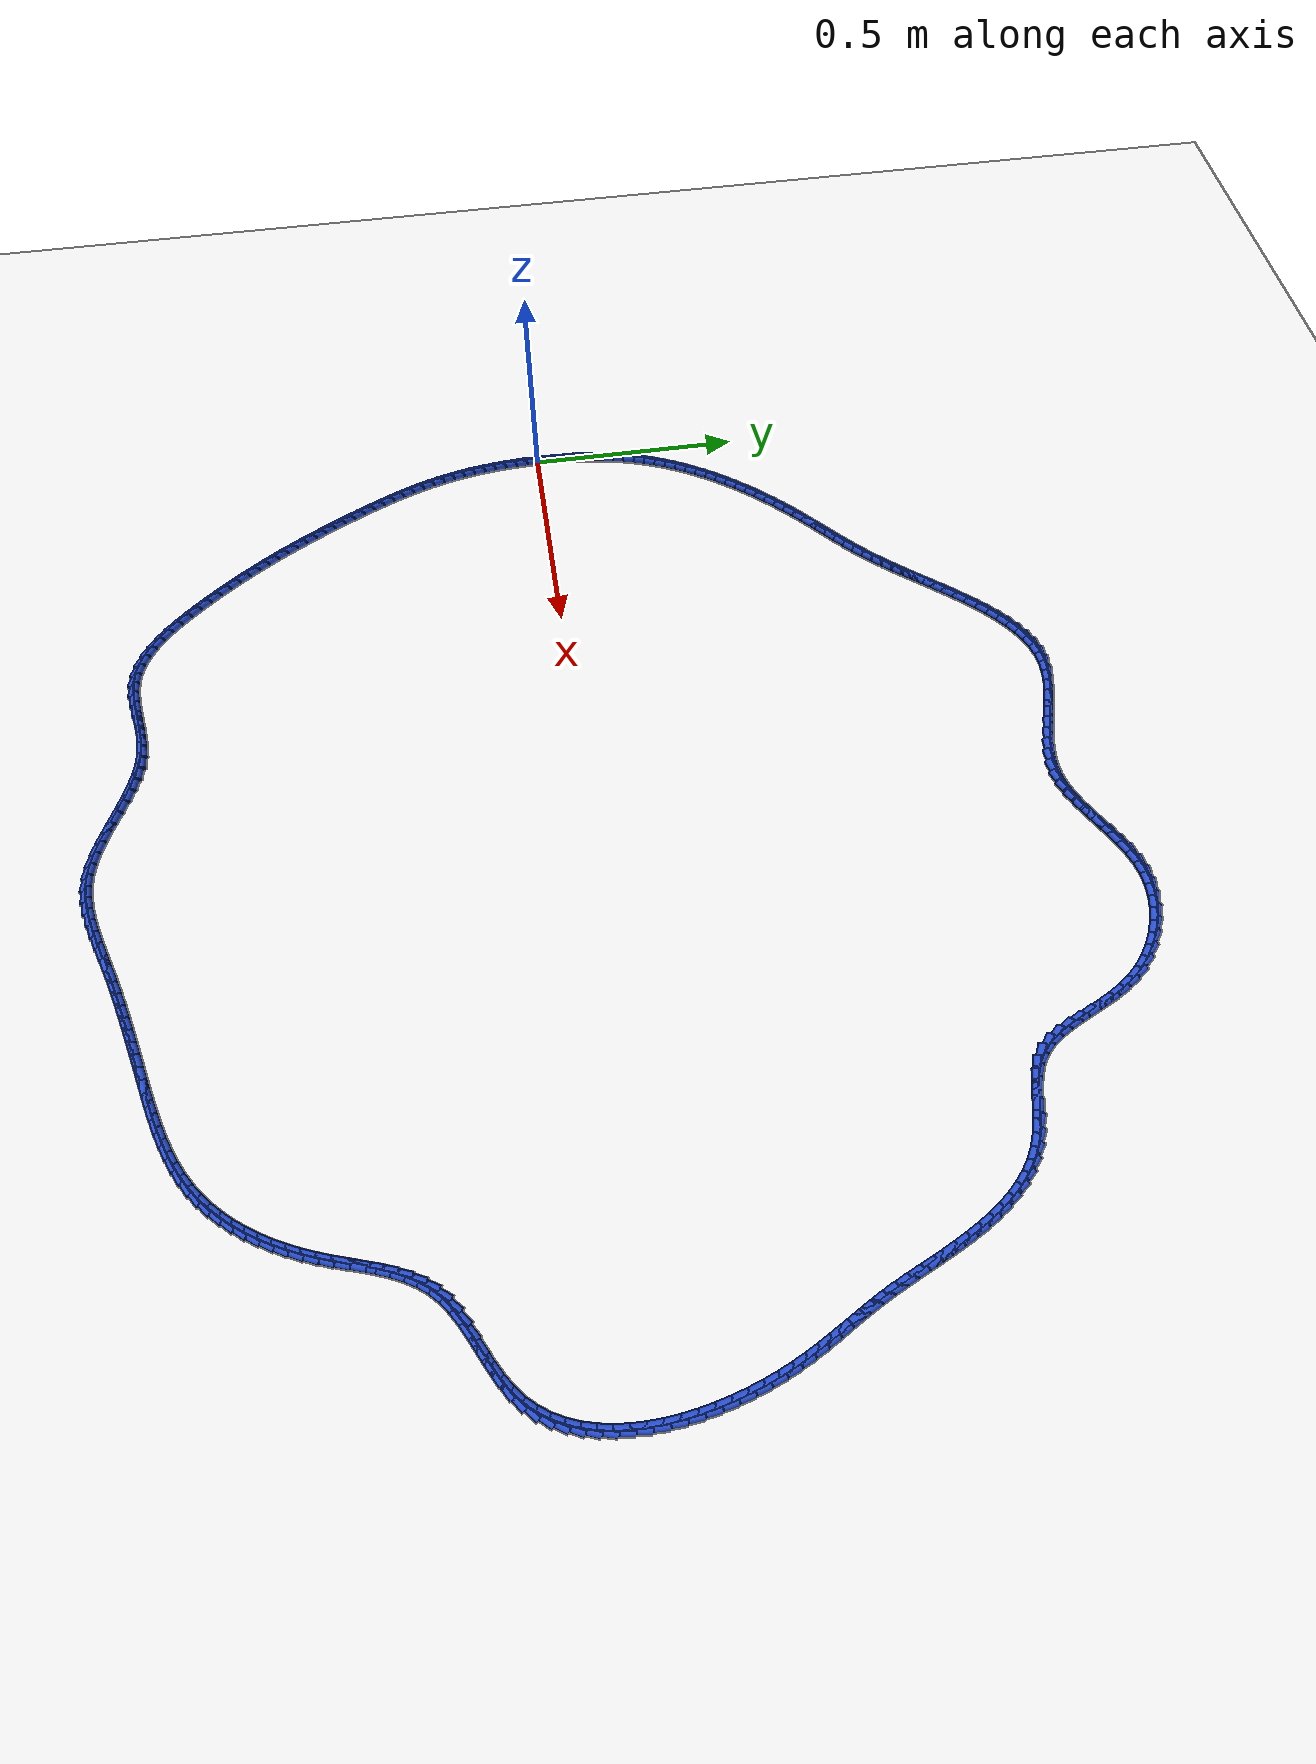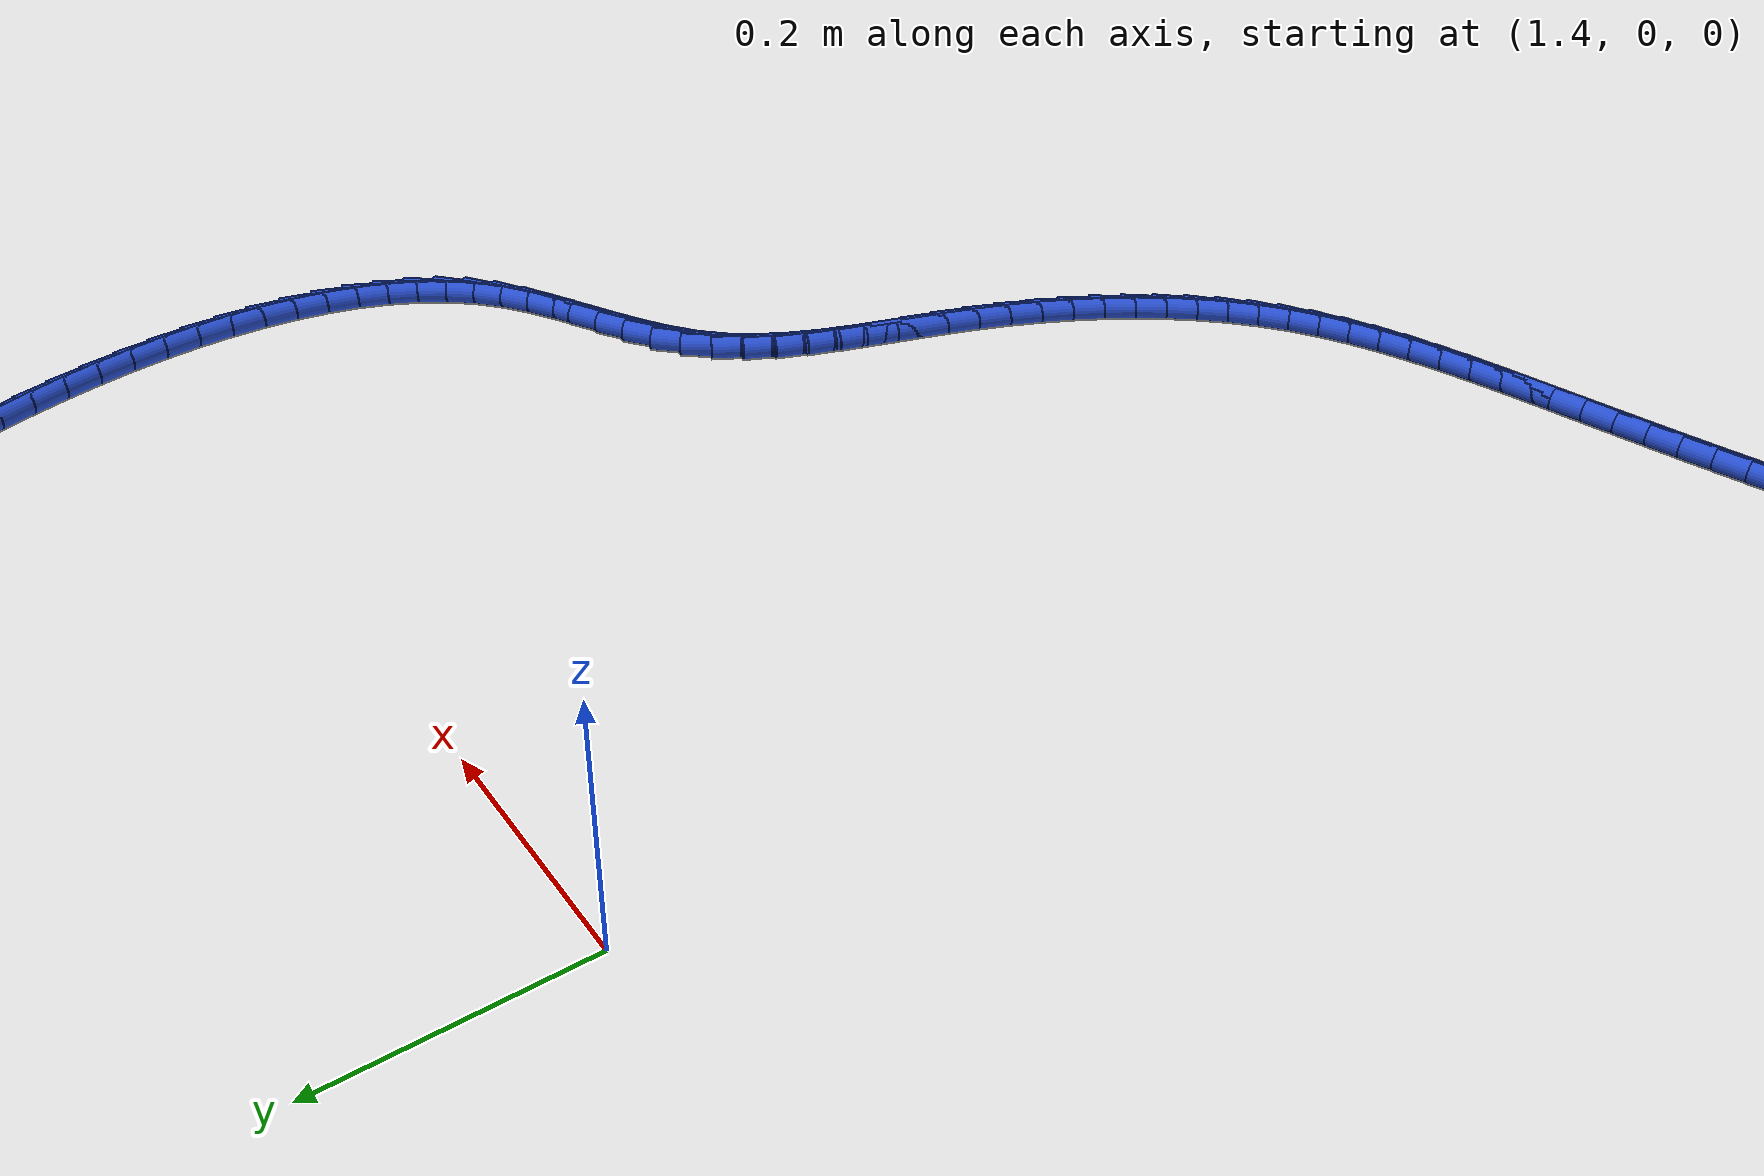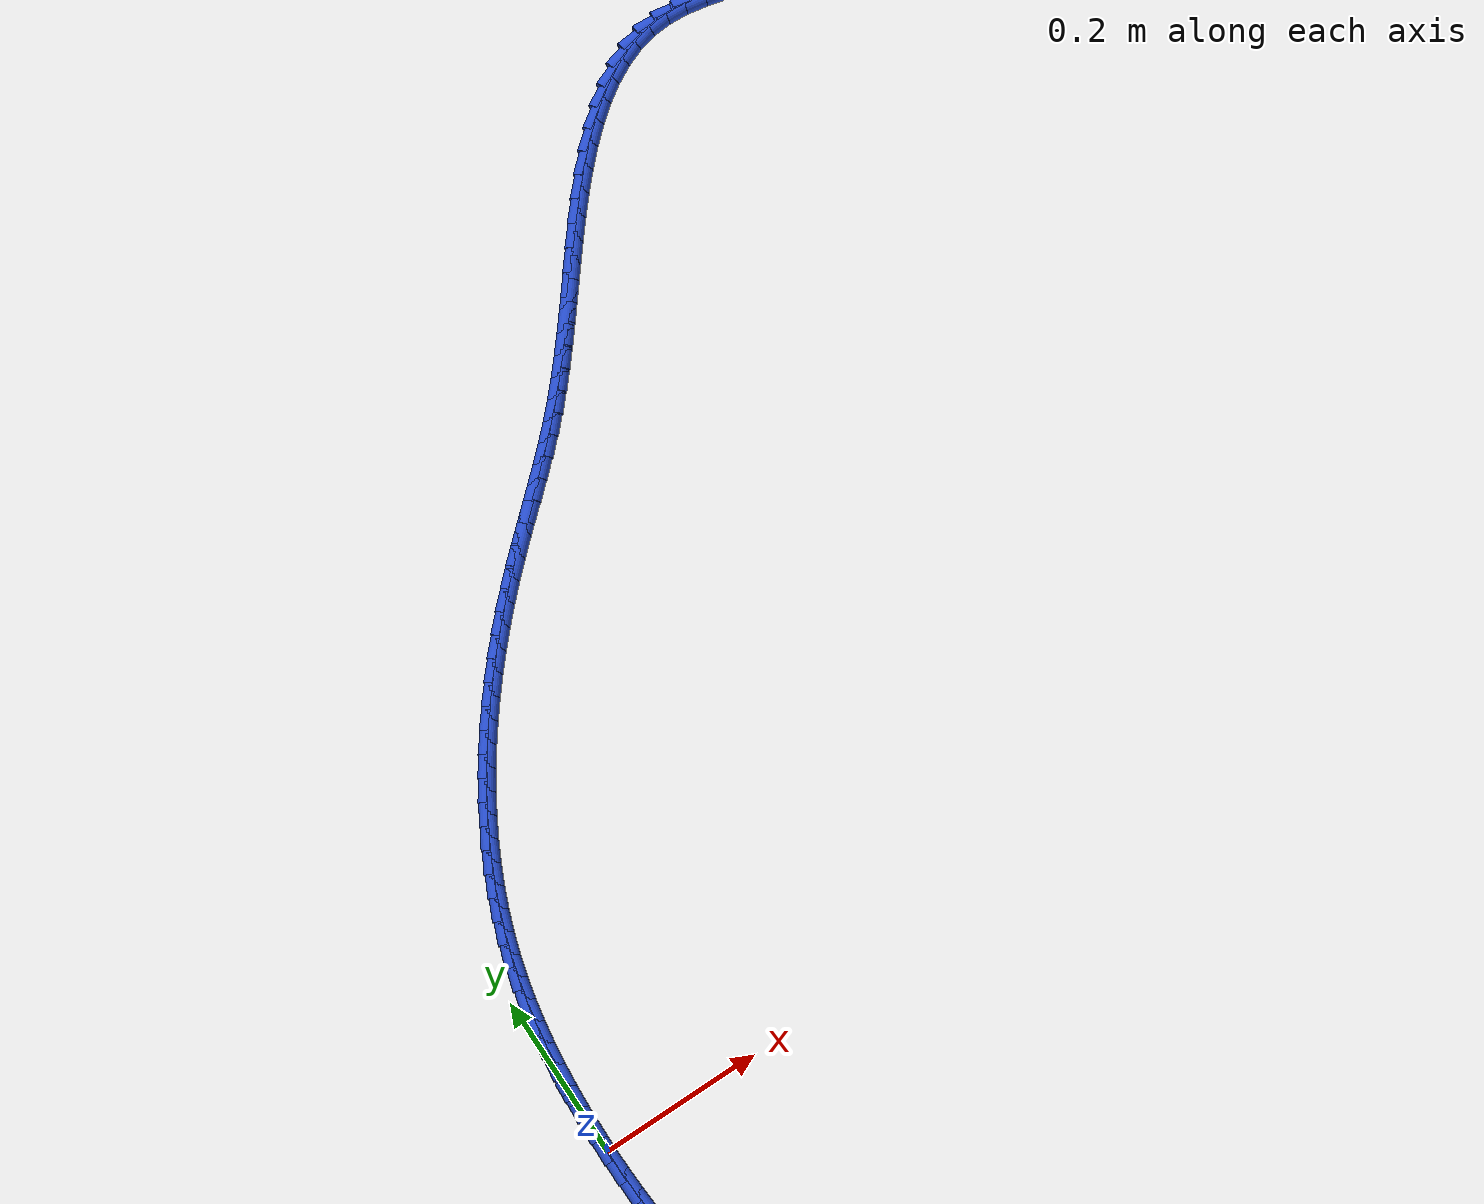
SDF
<sdf version="1.6">
 <world name="default">
  <light name="sun" type="directional">
   <pose>0 0 10 0 -0 0</pose>
   <diffuse>0.8 0.8 0.8 1</diffuse>
   <specular>0.2 0.2 0.2 1</specular>
   <attenuation>
    <range>1000</range>
    <constant>0.9</constant>
    <linear>0.01</linear>
    <quadratic>0.001</quadratic>
   </attenuation>
   <direction>-0.5 0.1 -0.9</direction>
  </light>
  <model name="ground_plane">
   <static>1</static>
   <link name="link">
    <collision name="collision">
     <geometry><plane><normal>0 0 1</normal><size>100 100</size></plane></geometry>
     <surface><friction><ode><mu>100</mu><mu2>50</mu2></ode></friction></surface>
    </collision>
    <visual name="visual">
     <cast_shadows>0</cast_shadows>
     <geometry><plane><normal>0 0 1</normal><size>100 100</size></plane></geometry>
     <material>
      <script><uri>file://media/materials/scripts/gazebo.material</uri><name>Gazebo/WhiteGlow</name></script>
     </material>
    </visual>
   </link>
  </model>
  <gravity>0 0 -9.8</gravity>
  <magnetic_field>6e-06 2.3e-05 -4.2e-05</magnetic_field>
  <atmosphere type="adiabatic"/>
  <physics name="default_physics" default="0" type="ode">
   <max_step_size>0.001</max_step_size>
   <real_time_factor>1</real_time_factor>
   <real_time_update_rate>1000</real_time_update_rate>
  </physics>
  <scene><ambient>0.4 0.4 0.4 1</ambient><background>0.7 0.7 0.7 1</background><shadows>1</shadows></scene>
  <spherical_coordinates>
   <surface_model>EARTH_WGS84</surface_model>
   <latitude_deg>0</latitude_deg>
   <longitude_deg>0</longitude_deg>
   <elevation>0</elevation>
   <heading_deg>0</heading_deg>
  </spherical_coordinates>
  <model name="line">
   <link name="link_0">
    <pose>8.673617379884035e-18 -2.0816681711721685e-17 0.01 0 1.57 1.5663600836026919</pose>
    <collision name="collision">
     <geometry><cylinder><radius>0.01</radius><length>0.08</length></cylinder></geometry>
    </collision>
    <visual name="visual">
     <material>
      <script><name>Gazebo/Blue</name><uri>file://media/materials/scripts/gazebo.material</uri></script>
     </material>
     <geometry><cylinder><radius>0.01</radius><length>0.08</length></cylinder></geometry>
    </visual>
   </link>
   <link name="link_1">
    <pose>0.00012192566793936917 0.027483810695920288 0.01 0 1.57 1.5422133245262204</pose>
    <collision name="collision">
     <geometry><cylinder><radius>0.01</radius><length>0.08</length></cylinder></geometry>
    </collision>
    <visual name="visual">
     <material>
      <script><name>Gazebo/Blue</name><uri>file://media/materials/scripts/gazebo.material</uri></script>
     </material>
     <geometry><cylinder><radius>0.01</radius><length>0.08</length></cylinder></geometry>
    </visual>
   </link>
   <link name="link_2">
    <pose>0.0009075358514911203 0.05496154798233627 0.01 0 1.57 1.5158821200807908</pose>
    <collision name="collision">
     <geometry><cylinder><radius>0.01</radius><length>0.08</length></cylinder></geometry>
    </collision>
    <visual name="visual">
     <material>
      <script><name>Gazebo/Blue</name><uri>file://media/materials/scripts/gazebo.material</uri></script>
     </material>
     <geometry><cylinder><radius>0.01</radius><length>0.08</length></cylinder></geometry>
    </visual>
   </link>
   <link name="link_3">
    <pose>0.0024153194357329987 0.08239101952638368 0.01 0 1.57 1.4872847770047268</pose>
    <collision name="collision">
     <geometry><cylinder><radius>0.01</radius><length>0.08</length></cylinder></geometry>
    </collision>
    <visual name="visual">
     <material>
      <script><name>Gazebo/Blue</name><uri>file://media/materials/scripts/gazebo.material</uri></script>
     </material>
     <geometry><cylinder><radius>0.01</radius><length>0.08</length></cylinder></geometry>
    </visual>
   </link>
   <link name="link_4">
    <pose>0.004703765305742742 0.10973003299519836 0.01 0 1.57 1.4563404634031636</pose>
    <collision name="collision">
     <geometry><cylinder><radius>0.01</radius><length>0.08</length></cylinder></geometry>
    </collision>
    <visual name="visual">
     <material>
      <script><name>Gazebo/Blue</name><uri>file://media/materials/scripts/gazebo.material</uri></script>
     </material>
     <geometry><cylinder><radius>0.01</radius><length>0.08</length></cylinder></geometry>
    </visual>
   </link>
   <link name="link_5">
    <pose>0.007831362346598085 0.13693639605591607 0.01 0 1.57 1.4229735264105285</pose>
    <collision name="collision">
     <geometry><cylinder><radius>0.01</radius><length>0.08</length></cylinder></geometry>
    </collision>
    <visual name="visual">
     <material>
      <script><name>Gazebo/Blue</name><uri>file://media/materials/scripts/gazebo.material</uri></script>
     </material>
     <geometry><cylinder><radius>0.01</radius><length>0.08</length></cylinder></geometry>
    </visual>
   </link>
   <link name="link_6">
    <pose>0.011856599443376758 0.16396791637567254 0.01 0 1.57 1.3871187343726636</pose>
    <collision name="collision">
     <geometry><cylinder><radius>0.01</radius><length>0.08</length></cylinder></geometry>
    </collision>
    <visual name="visual">
     <material>
      <script><name>Gazebo/Blue</name><uri>file://media/materials/scripts/gazebo.material</uri></script>
     </material>
     <geometry><cylinder><radius>0.01</radius><length>0.08</length></cylinder></geometry>
    </visual>
   </link>
   <link name="link_7">
    <pose>0.0168379654811565 0.19078240162160356 0.01 0 1.57 1.348727491570695</pose>
    <collision name="collision">
     <geometry><cylinder><radius>0.01</radius><length>0.08</length></cylinder></geometry>
    </collision>
    <visual name="visual">
     <material>
      <script><name>Gazebo/Blue</name><uri>file://media/materials/scripts/gazebo.material</uri></script>
     </material>
     <geometry><cylinder><radius>0.01</radius><length>0.08</length></cylinder></geometry>
    </visual>
   </link>
   <link name="link_8">
    <pose>0.022833949345015057 0.2173376594608451 0.01 0 1.57 1.30777497485197</pose>
    <collision name="collision">
     <geometry><cylinder><radius>0.01</radius><length>0.08</length></cylinder></geometry>
    </collision>
    <visual name="visual">
     <material>
      <script><name>Gazebo/Blue</name><uri>file://media/materials/scripts/gazebo.material</uri></script>
     </material>
     <geometry><cylinder><radius>0.01</radius><length>0.08</length></cylinder></geometry>
    </visual>
   </link>
   <link name="link_9">
    <pose>0.029903039920030156 0.24359149756053275 0.01 0 1.57 1.2646253186359724</pose>
    <collision name="collision">
     <geometry><cylinder><radius>0.01</radius><length>0.08</length></cylinder></geometry>
    </collision>
    <visual name="visual">
     <material>
      <script><name>Gazebo/Blue</name><uri>file://media/materials/scripts/gazebo.material</uri></script>
     </material>
     <geometry><cylinder><radius>0.01</radius><length>0.08</length></cylinder></geometry>
    </visual>
   </link>
   <link name="link_10">
    <pose>0.03809444601554173 0.2695045849948197 0.01 0 1.57 1.221922487475589</pose>
    <collision name="collision">
     <geometry><cylinder><radius>0.01</radius><length>0.08</length></cylinder></geometry>
    </collision>
    <visual name="visual">
     <material>
      <script><name>Gazebo/Blue</name><uri>file://media/materials/scripts/gazebo.material</uri></script>
     </material>
     <geometry><cylinder><radius>0.01</radius><length>0.08</length></cylinder></geometry>
    </visual>
   </link>
   <link name="link_11">
    <pose>0.04738973502929857 0.295058447306627 0.01 0 1.57 1.1808572579565573</pose>
    <collision name="collision">
     <geometry><cylinder><radius>0.01</radius><length>0.08</length></cylinder></geometry>
    </collision>
    <visual name="visual">
     <material>
      <script><name>Gazebo/Blue</name><uri>file://media/materials/scripts/gazebo.material</uri></script>
     </material>
     <geometry><cylinder><radius>0.01</radius><length>0.08</length></cylinder></geometry>
    </visual>
   </link>
   <link name="link_12">
    <pose>0.057740522825169845 0.32024384525760086 0.01 0 1.57 1.141448639702506</pose>
    <collision name="collision">
     <geometry><cylinder><radius>0.01</radius><length>0.08</length></cylinder></geometry>
    </collision>
    <visual name="visual">
     <material>
      <script><name>Gazebo/Blue</name><uri>file://media/materials/scripts/gazebo.material</uri></script>
     </material>
     <geometry><cylinder><radius>0.01</radius><length>0.08</length></cylinder></geometry>
    </visual>
   </link>
   <link name="link_13">
    <pose>0.06909829164547844 0.3450515808100888 0.01 0 1.57 1.1036890187400088</pose>
    <collision name="collision">
     <geometry><cylinder><radius>0.01</radius><length>0.08</length></cylinder></geometry>
    </collision>
    <visual name="visual">
     <material>
      <script><name>Gazebo/Blue</name><uri>file://media/materials/scripts/gazebo.material</uri></script>
     </material>
     <geometry><cylinder><radius>0.01</radius><length>0.08</length></cylinder></geometry>
    </visual>
   </link>
   <link name="link_14">
    <pose>0.08141452373254733 0.36947245592643835 0.01 0 1.57 1.0675528361045028</pose>
    <collision name="collision">
     <geometry><cylinder><radius>0.01</radius><length>0.08</length></cylinder></geometry>
    </collision>
    <visual name="visual">
     <material>
      <script><name>Gazebo/Blue</name><uri>file://media/materials/scripts/gazebo.material</uri></script>
     </material>
     <geometry><cylinder><radius>0.01</radius><length>0.08</length></cylinder></geometry>
    </visual>
   </link>
   <link name="link_15">
    <pose>0.09464070132869941 0.3934972725689971 0.01 0 1.57 1.032999993604707</pose>
    <collision name="collision">
     <geometry><cylinder><radius>0.01</radius><length>0.08</length></cylinder></geometry>
    </collision>
    <visual name="visual">
     <material>
      <script><name>Gazebo/Blue</name><uri>file://media/materials/scripts/gazebo.material</uri></script>
     </material>
     <geometry><cylinder><radius>0.01</radius><length>0.08</length></cylinder></geometry>
    </visual>
   </link>
   <link name="link_16">
    <pose>0.10872830667625771 0.4171168327001126 0.01 0 1.57 0.9999789948081577</pose>
    <collision name="collision">
     <geometry><cylinder><radius>0.01</radius><length>0.08</length></cylinder></geometry>
    </collision>
    <visual name="visual">
     <material>
      <script><name>Gazebo/Blue</name><uri>file://media/materials/scripts/gazebo.material</uri></script>
     </material>
     <geometry><cylinder><radius>0.01</radius><length>0.08</length></cylinder></geometry>
    </visual>
   </link>
   <link name="link_17">
    <pose>0.1236288220175451 0.44032193828213245 0.01 0 1.57 0.9684297389983882</pose>
    <collision name="collision">
     <geometry><cylinder><radius>0.01</radius><length>0.08</length></cylinder></geometry>
    </collision>
    <visual name="visual">
     <material>
      <script><name>Gazebo/Blue</name><uri>file://media/materials/scripts/gazebo.material</uri></script>
     </material>
     <geometry><cylinder><radius>0.01</radius><length>0.08</length></cylinder></geometry>
    </visual>
   </link>
   <link name="link_18">
    <pose>0.1392937295948845 0.46310339127740424 0.01 0 1.57 0.9382859299687416</pose>
    <collision name="collision">
     <geometry><cylinder><radius>0.01</radius><length>0.08</length></cylinder></geometry>
    </collision>
    <visual name="visual">
     <material>
      <script><name>Gazebo/Blue</name><uri>file://media/materials/scripts/gazebo.material</uri></script>
     </material>
     <geometry><cylinder><radius>0.01</radius><length>0.08</length></cylinder></geometry>
    </visual>
   </link>
   <link name="link_19">
    <pose>0.15567451165059892 0.48545199364827557 0.01 0 1.57 0.909477094309164</pose>
    <collision name="collision">
     <geometry><cylinder><radius>0.01</radius><length>0.08</length></cylinder></geometry>
    </collision>
    <visual name="visual">
     <material>
      <script><name>Gazebo/Blue</name><uri>file://media/materials/scripts/gazebo.material</uri></script>
     </material>
     <geometry><cylinder><radius>0.01</radius><length>0.08</length></cylinder></geometry>
    </visual>
   </link>
   <link name="link_20">
    <pose>0.17272265042701124 0.5073585473570938 0.01 0 1.57 0.8819302261880976</pose>
    <collision name="collision">
     <geometry><cylinder><radius>0.01</radius><length>0.08</length></cylinder></geometry>
    </collision>
    <visual name="visual">
     <material>
      <script><name>Gazebo/Blue</name><uri>file://media/materials/scripts/gazebo.material</uri></script>
     </material>
     <geometry><cylinder><radius>0.01</radius><length>0.08</length></cylinder></geometry>
    </visual>
   </link>
   <link name="link_21">
    <pose>0.1903896281664445 0.5288138543662069 0.01 0 1.57 0.8555710892377606</pose>
    <collision name="collision">
     <geometry><cylinder><radius>0.01</radius><length>0.08</length></cylinder></geometry>
    </collision>
    <visual name="visual">
     <material>
      <script><name>Gazebo/Blue</name><uri>file://media/materials/scripts/gazebo.material</uri></script>
     </material>
     <geometry><cylinder><radius>0.01</radius><length>0.08</length></cylinder></geometry>
    </visual>
   </link>
   <link name="link_22">
    <pose>0.20862692711122144 0.5498087166379619 0.01 0 1.57 0.8303252129808268</pose>
    <collision name="collision">
     <geometry><cylinder><radius>0.01</radius><length>0.08</length></cylinder></geometry>
    </collision>
    <visual name="visual">
     <material>
      <script><name>Gazebo/Blue</name><uri>file://media/materials/scripts/gazebo.material</uri></script>
     </material>
     <geometry><cylinder><radius>0.01</radius><length>0.08</length></cylinder></geometry>
    </visual>
   </link>
   <link name="link_23">
    <pose>0.22738602950366515 0.5703339361347067 0.01 0 1.57 0.8061186231546273</pose>
    <collision name="collision">
     <geometry><cylinder><radius>0.01</radius><length>0.08</length></cylinder></geometry>
    </collision>
    <visual name="visual">
     <material>
      <script><name>Gazebo/Blue</name><uri>file://media/materials/scripts/gazebo.material</uri></script>
     </material>
     <geometry><cylinder><radius>0.01</radius><length>0.08</length></cylinder></geometry>
    </visual>
   </link>
   <link name="link_24">
    <pose>0.24661841758609862 0.5903803148187889 0.01 0 1.57 0.7828783438797636</pose>
    <collision name="collision">
     <geometry><cylinder><radius>0.01</radius><length>0.08</length></cylinder></geometry>
    </collision>
    <visual name="visual">
     <material>
      <script><name>Gazebo/Blue</name><uri>file://media/materials/scripts/gazebo.material</uri></script>
     </material>
     <geometry><cylinder><radius>0.01</radius><length>0.08</length></cylinder></geometry>
    </visual>
   </link>
   <link name="link_25">
    <pose>0.2662755736008447 0.609938654652556 0.01 0 1.57 0.7609730513658597</pose>
    <collision name="collision">
     <geometry><cylinder><radius>0.01</radius><length>0.08</length></cylinder></geometry>
    </collision>
    <visual name="visual">
     <material>
      <script><name>Gazebo/Blue</name><uri>file://media/materials/scripts/gazebo.material</uri></script>
     </material>
     <geometry><cylinder><radius>0.01</radius><length>0.08</length></cylinder></geometry>
    </visual>
   </link>
   <link name="link_26">
    <pose>0.28630177495491677 0.6290097111537828 0.01 0 1.57 0.7443623579335109</pose>
    <collision name="collision">
     <geometry><cylinder><radius>0.01</radius><length>0.08</length></cylinder></geometry>
    </collision>
    <visual name="visual">
     <material>
      <script><name>Gazebo/Blue</name><uri>file://media/materials/scripts/gazebo.material</uri></script>
     </material>
     <geometry><cylinder><radius>0.01</radius><length>0.08</length></cylinder></geometry>
    </visual>
   </link>
   <link name="link_27">
    <pose>0.3065758810578792 0.6476846154887604 0.01 0 1.57 0.7352147930448082</pose>
    <collision name="collision">
     <geometry><cylinder><radius>0.01</radius><length>0.08</length></cylinder></geometry>
    </collision>
    <visual name="visual">
     <material>
      <script><name>Gazebo/Blue</name><uri>file://media/materials/scripts/gazebo.material</uri></script>
     </material>
     <geometry><cylinder><radius>0.01</radius><length>0.08</length></cylinder></geometry>
    </visual>
   </link>
   <link name="link_28">
    <pose>0.3269418840385629 0.6661026683372335 0.01 0 1.57 0.7336184679128666</pose>
    <collision name="collision">
     <geometry><cylinder><radius>0.01</radius><length>0.08</length></cylinder></geometry>
    </collision>
    <visual name="visual">
     <material>
      <script><name>Gazebo/Blue</name><uri>file://media/materials/scripts/gazebo.material</uri></script>
     </material>
     <geometry><cylinder><radius>0.01</radius><length>0.08</length></cylinder></geometry>
    </visual>
   </link>
   <link name="link_29">
    <pose>0.34724345059569356 0.684403619964046 0.01 0 1.57 0.7396749762467577</pose>
    <collision name="collision">
     <geometry><cylinder><radius>0.01</radius><length>0.08</length></cylinder></geometry>
    </collision>
    <visual name="visual">
     <material>
      <script><name>Gazebo/Blue</name><uri>file://media/materials/scripts/gazebo.material</uri></script>
     </material>
     <geometry><cylinder><radius>0.01</radius><length>0.08</length></cylinder></geometry>
    </visual>
   </link>
   <link name="link_30">
    <pose>0.36732424742799646 0.7027272206340414 0.01 0 1.57 0.7535235582046028</pose>
    <collision name="collision">
     <geometry><cylinder><radius>0.01</radius><length>0.08</length></cylinder></geometry>
    </collision>
    <visual name="visual">
     <material>
      <script><name>Gazebo/Blue</name><uri>file://media/materials/scripts/gazebo.material</uri></script>
     </material>
     <geometry><cylinder><radius>0.01</radius><length>0.08</length></cylinder></geometry>
    </visual>
   </link>
   <link name="link_31">
    <pose>0.38702794123419726 0.7212132206120635 0.01 0 1.57 0.7753320133204081</pose>
    <collision name="collision">
     <geometry><cylinder><radius>0.01</radius><length>0.08</length></cylinder></geometry>
    </collision>
    <visual name="visual">
     <material>
      <script><name>Gazebo/Blue</name><uri>file://media/materials/scripts/gazebo.material</uri></script>
     </material>
     <geometry><cylinder><radius>0.01</radius><length>0.08</length></cylinder></geometry>
    </visual>
   </link>
   <link name="link_32">
    <pose>0.40619819871302126 0.7400013701629558 0.01 0 1.57 0.8042390803187631</pose>
    <collision name="collision">
     <geometry><cylinder><radius>0.01</radius><length>0.08</length></cylinder></geometry>
    </collision>
    <visual name="visual">
     <material>
      <script><name>Gazebo/Blue</name><uri>file://media/materials/scripts/gazebo.material</uri></script>
     </material>
     <geometry><cylinder><radius>0.01</radius><length>0.08</length></cylinder></geometry>
    </visual>
   </link>
   <link name="link_33">
    <pose>0.4247084359366143 0.7592225867020511 0.01 0 1.57 0.8324504869114397</pose>
    <collision name="collision">
     <geometry><cylinder><radius>0.01</radius><length>0.08</length></cylinder></geometry>
    </collision>
    <visual name="visual">
     <material>
      <script><name>Gazebo/Blue</name><uri>file://media/materials/scripts/gazebo.material</uri></script>
     </material>
     <geometry><cylinder><radius>0.01</radius><length>0.08</length></cylinder></geometry>
    </visual>
   </link>
   <link name="link_34">
    <pose>0.44265416155738607 0.7789418464125376 0.01 0 1.57 0.8560008965633754</pose>
    <collision name="collision">
     <geometry><cylinder><radius>0.01</radius><length>0.08</length></cylinder></geometry>
    </collision>
    <visual name="visual">
     <material>
      <script><name>Gazebo/Blue</name><uri>file://media/materials/scripts/gazebo.material</uri></script>
     </material>
     <geometry><cylinder><radius>0.01</radius><length>0.08</length></cylinder></geometry>
    </visual>
   </link>
   <link name="link_35">
    <pose>0.46023130458858236 0.7991943097929985 0.01 0 1.57 0.8745176464956673</pose>
    <collision name="collision">
     <geometry><cylinder><radius>0.01</radius><length>0.08</length></cylinder></geometry>
    </collision>
    <visual name="visual">
     <material>
      <script><name>Gazebo/Blue</name><uri>file://media/materials/scripts/gazebo.material</uri></script>
     </material>
     <geometry><cylinder><radius>0.01</radius><length>0.08</length></cylinder></geometry>
    </visual>
   </link>
   <link name="link_36">
    <pose>0.47763628684318526 0.8200149910254603 0.01 0 1.57 0.8878527197833259</pose>
    <collision name="collision">
     <geometry><cylinder><radius>0.01</radius><length>0.08</length></cylinder></geometry>
    </collision>
    <visual name="visual">
     <material>
      <script><name>Gazebo/Blue</name><uri>file://media/materials/scripts/gazebo.material</uri></script>
     </material>
     <geometry><cylinder><radius>0.01</radius><length>0.08</length></cylinder></geometry>
    </visual>
   </link>
   <link name="link_37">
    <pose>0.4950655301341765 0.8414389042919485 0.01 0 1.57 0.8960498969316935</pose>
    <collision name="collision">
     <geometry><cylinder><radius>0.01</radius><length>0.08</length></cylinder></geometry>
    </collision>
    <visual name="visual">
     <material>
      <script><name>Gazebo/Blue</name><uri>file://media/materials/scripts/gazebo.material</uri></script>
     </material>
     <geometry><cylinder><radius>0.01</radius><length>0.08</length></cylinder></geometry>
    </visual>
   </link>
   <link name="link_38">
    <pose>0.5127154562745383 0.8635010637744898 0.01 0 1.57 0.8990206559172321</pose>
    <collision name="collision">
     <geometry><cylinder><radius>0.01</radius><length>0.08</length></cylinder></geometry>
    </collision>
    <visual name="visual">
     <material>
      <script><name>Gazebo/Blue</name><uri>file://media/materials/scripts/gazebo.material</uri></script>
     </material>
     <geometry><cylinder><radius>0.01</radius><length>0.08</length></cylinder></geometry>
    </visual>
   </link>
   <link name="link_39">
    <pose>0.5307695481734757 0.886206373588862 0.01 0 1.57 0.8946504027893772</pose>
    <collision name="collision">
     <geometry><cylinder><radius>0.01</radius><length>0.08</length></cylinder></geometry>
    </collision>
    <visual name="visual">
     <material>
      <script><name>Gazebo/Blue</name><uri>file://media/materials/scripts/gazebo.material</uri></script>
     </material>
     <geometry><cylinder><radius>0.01</radius><length>0.08</length></cylinder></geometry>
    </visual>
   </link>
   <link name="link_40">
    <pose>0.5493019269409729 0.9093052424873804 0.01 0 1.57 0.8820267981212863</pose>
    <collision name="collision">
     <geometry><cylinder><radius>0.01</radius><length>0.08</length></cylinder></geometry>
    </collision>
    <visual name="visual">
     <material>
      <script><name>Gazebo/Blue</name><uri>file://media/materials/scripts/gazebo.material</uri></script>
     </material>
     <geometry><cylinder><radius>0.01</radius><length>0.08</length></cylinder></geometry>
    </visual>
   </link>
   <link name="link_41">
    <pose>0.5683317543818567 0.9324201836643005 0.01 0 1.57 0.8610606553677093</pose>
    <collision name="collision">
     <geometry><cylinder><radius>0.01</radius><length>0.08</length></cylinder></geometry>
    </collision>
    <visual name="visual">
     <material>
      <script><name>Gazebo/Blue</name><uri>file://media/materials/scripts/gazebo.material</uri></script>
     </material>
     <geometry><cylinder><radius>0.01</radius><length>0.08</length></cylinder></geometry>
    </visual>
   </link>
   <link name="link_42">
    <pose>0.5878777768841583 0.9551727435992726 0.01 0 1.57 0.8312353115284545</pose>
    <collision name="collision">
     <geometry><cylinder><radius>0.01</radius><length>0.08</length></cylinder></geometry>
    </collision>
    <visual name="visual">
     <material>
      <script><name>Gazebo/Blue</name><uri>file://media/materials/scripts/gazebo.material</uri></script>
     </material>
     <geometry><cylinder><radius>0.01</radius><length>0.08</length></cylinder></geometry>
    </visual>
   </link>
   <link name="link_43">
    <pose>0.6079587408359077 0.9771844687719466 0.01 0 1.57 0.7916057208700408</pose>
    <collision name="collision">
     <geometry><cylinder><radius>0.01</radius><length>0.08</length></cylinder></geometry>
    </collision>
    <visual name="visual">
     <material>
      <script><name>Gazebo/Blue</name><uri>file://media/materials/scripts/gazebo.material</uri></script>
     </material>
     <geometry><cylinder><radius>0.01</radius><length>0.08</length></cylinder></geometry>
    </visual>
   </link>
   <link name="link_44">
    <pose>0.6285933926251355 0.9980769056619727 0.01 0 1.57 0.7407895638793492</pose>
    <collision name="collision">
     <geometry><cylinder><radius>0.01</radius><length>0.08</length></cylinder></geometry>
    </collision>
    <visual name="visual">
     <material>
      <script><name>Gazebo/Blue</name><uri>file://media/materials/scripts/gazebo.material</uri></script>
     </material>
     <geometry><cylinder><radius>0.01</radius><length>0.08</length></cylinder></geometry>
    </visual>
   </link>
   <link name="link_45">
    <pose>0.6498004786398724 1.0174716007490014 0.01 0 1.57 0.6769715897637685</pose>
    <collision name="collision">
     <geometry><cylinder><radius>0.01</radius><length>0.08</length></cylinder></geometry>
    </collision>
    <visual name="visual">
     <material>
      <script><name>Gazebo/Blue</name><uri>file://media/materials/scripts/gazebo.material</uri></script>
     </material>
     <geometry><cylinder><radius>0.01</radius><length>0.08</length></cylinder></geometry>
    </visual>
   </link>
   <link name="link_46">
    <pose>0.6715987452681489 1.0349901005126823 0.01 0 1.57 0.5979781573252401</pose>
    <collision name="collision">
     <geometry><cylinder><radius>0.01</radius><length>0.08</length></cylinder></geometry>
    </collision>
    <visual name="visual">
     <material>
      <script><name>Gazebo/Blue</name><uri>file://media/materials/scripts/gazebo.material</uri></script>
     </material>
     <geometry><cylinder><radius>0.01</radius><length>0.08</length></cylinder></geometry>
    </visual>
   </link>
   <link name="link_47">
    <pose>0.6940069388979957 1.0502539514326656 0.01 0 1.57 0.50152488870363</pose>
    <collision name="collision">
     <geometry><cylinder><radius>0.01</radius><length>0.08</length></cylinder></geometry>
    </collision>
    <visual name="visual">
     <material>
      <script><name>Gazebo/Blue</name><uri>file://media/materials/scripts/gazebo.material</uri></script>
     </material>
     <geometry><cylinder><radius>0.01</radius><length>0.08</length></cylinder></geometry>
    </visual>
   </link>
   <link name="link_48">
    <pose>0.7170438059174431 1.0628846999886021 0.01 0 1.57 0.38579029363609757</pose>
    <collision name="collision">
     <geometry><cylinder><radius>0.01</radius><length>0.08</length></cylinder></geometry>
    </collision>
    <visual name="visual">
     <material>
      <script><name>Gazebo/Blue</name><uri>file://media/materials/scripts/gazebo.material</uri></script>
     </material>
     <geometry><cylinder><radius>0.01</radius><length>0.08</length></cylinder></geometry>
    </visual>
   </link>
   <link name="link_49">
    <pose>0.7407280927145217 1.0725038926601407 0.01 0 1.57 0.2504429980740751</pose>
    <collision name="collision">
     <geometry><cylinder><radius>0.01</radius><length>0.08</length></cylinder></geometry>
    </collision>
    <visual name="visual">
     <material>
      <script><name>Gazebo/Blue</name><uri>file://media/materials/scripts/gazebo.material</uri></script>
     </material>
     <geometry><cylinder><radius>0.01</radius><length>0.08</length></cylinder></geometry>
    </visual>
   </link>
   <link name="link_50">
    <pose>0.765078545677262 1.078733075926932 0.01 0 1.57 0.09814398672746759</pose>
    <collision name="collision">
     <geometry><cylinder><radius>0.01</radius><length>0.08</length></cylinder></geometry>
    </collision>
    <visual name="visual">
     <material>
      <script><name>Gazebo/Blue</name><uri>file://media/materials/scripts/gazebo.material</uri></script>
     </material>
     <geometry><cylinder><radius>0.01</radius><length>0.08</length></cylinder></geometry>
    </visual>
   </link>
   <link name="link_51">
    <pose>0.7901134105706822 1.0811980167639141 0.01 0 1.57 -0.050436674000525275</pose>
    <collision name="collision">
     <geometry><cylinder><radius>0.01</radius><length>0.08</length></cylinder></geometry>
    </collision>
    <visual name="visual">
     <material>
      <script><name>Gazebo/Blue</name><uri>file://media/materials/scripts/gazebo.material</uri></script>
     </material>
     <geometry><cylinder><radius>0.01</radius><length>0.08</length></cylinder></geometry>
    </visual>
   </link>
   <link name="link_52">
    <pose>0.8158062652087489 1.0799010546813437 0.01 0 1.57 -0.16566280958489482</pose>
    <collision name="collision">
     <geometry><cylinder><radius>0.01</radius><length>0.08</length></cylinder></geometry>
    </collision>
    <visual name="visual">
     <material>
      <script><name>Gazebo/Blue</name><uri>file://media/materials/scripts/gazebo.material</uri></script>
     </material>
     <geometry><cylinder><radius>0.01</radius><length>0.08</length></cylinder></geometry>
    </visual>
   </link>
   <link name="link_53">
    <pose>0.8420513957010565 1.0755129967918837 0.01 0 1.57 -0.24740260322809296</pose>
    <collision name="collision">
     <geometry><cylinder><radius>0.01</radius><length>0.08</length></cylinder></geometry>
    </collision>
    <visual name="visual">
     <material>
      <script><name>Gazebo/Blue</name><uri>file://media/materials/scripts/gazebo.material</uri></script>
     </material>
     <geometry><cylinder><radius>0.01</radius><length>0.08</length></cylinder></geometry>
    </visual>
   </link>
   <link name="link_54">
    <pose>0.8687349395097339 1.0687733472664722 0.01 0 1.57 -0.29990383422102085</pose>
    <collision name="collision">
     <geometry><cylinder><radius>0.01</radius><length>0.08</length></cylinder></geometry>
    </collision>
    <visual name="visual">
     <material>
      <script><name>Gazebo/Blue</name><uri>file://media/materials/scripts/gazebo.material</uri></script>
     </material>
     <geometry><cylinder><radius>0.01</radius><length>0.08</length></cylinder></geometry>
    </visual>
   </link>
   <link name="link_55">
    <pose>0.8957430340969084 1.0604216102760462 0.01 0 1.57 -0.3267480335180344</pose>
    <collision name="collision">
     <geometry><cylinder><radius>0.01</radius><length>0.08</length></cylinder></geometry>
    </collision>
    <visual name="visual">
     <material>
      <script><name>Gazebo/Blue</name><uri>file://media/materials/scripts/gazebo.material</uri></script>
     </material>
     <geometry><cylinder><radius>0.01</radius><length>0.08</length></cylinder></geometry>
    </visual>
   </link>
   <link name="link_56">
    <pose>0.9229618169247074 1.051197289991542 0.01 0 1.57 -0.3300368344223274</pose>
    <collision name="collision">
     <geometry><cylinder><radius>0.01</radius><length>0.08</length></cylinder></geometry>
    </collision>
    <visual name="visual">
     <material>
      <script><name>Gazebo/Blue</name><uri>file://media/materials/scripts/gazebo.material</uri></script>
     </material>
     <geometry><cylinder><radius>0.01</radius><length>0.08</length></cylinder></geometry>
    </visual>
   </link>
   <link name="link_57">
    <pose>0.9502774254552588 1.0418398905838975 0.01 0 1.57 -0.31021563518638295</pose>
    <collision name="collision">
     <geometry><cylinder><radius>0.01</radius><length>0.08</length></cylinder></geometry>
    </collision>
    <visual name="visual">
     <material>
      <script><name>Gazebo/Blue</name><uri>file://media/materials/scripts/gazebo.material</uri></script>
     </material>
     <geometry><cylinder><radius>0.01</radius><length>0.08</length></cylinder></geometry>
    </visual>
   </link>
   <link name="link_58">
    <pose>0.9775759971506903 1.033088916224049 0.01 0 1.57 -0.2661040379252089</pose>
    <collision name="collision">
     <geometry><cylinder><radius>0.01</radius><length>0.08</length></cylinder></geometry>
    </collision>
    <visual name="visual">
     <material>
      <script><name>Gazebo/Blue</name><uri>file://media/materials/scripts/gazebo.material</uri></script>
     </material>
     <geometry><cylinder><radius>0.01</radius><length>0.08</length></cylinder></geometry>
    </visual>
   </link>
   <link name="link_59">
    <pose>1.0047436694731298 1.0256838710829341 0.01 0 1.57 -0.1950741033738589</pose>
    <collision name="collision">
     <geometry><cylinder><radius>0.01</radius><length>0.08</length></cylinder></geometry>
    </collision>
    <visual name="visual">
     <material>
      <script><name>Gazebo/Blue</name><uri>file://media/materials/scripts/gazebo.material</uri></script>
     </material>
     <geometry><cylinder><radius>0.01</radius><length>0.08</length></cylinder></geometry>
    </visual>
   </link>
   <link name="link_60">
    <pose>1.0316665798847044 1.0203642593314894 0.01 0 1.57 -0.09363620932525915</pose>
    <collision name="collision">
     <geometry><cylinder><radius>0.01</radius><length>0.08</length></cylinder></geometry>
    </collision>
    <visual name="visual">
     <material>
      <script><name>Gazebo/Blue</name><uri>file://media/materials/scripts/gazebo.material</uri></script>
     </material>
     <geometry><cylinder><radius>0.01</radius><length>0.08</length></cylinder></geometry>
    </visual>
   </link>
   <link name="link_61">
    <pose>1.0582308658475426 1.0178695851406523 0.01 0 1.57 0.04097719420939117</pose>
    <collision name="collision">
     <geometry><cylinder><radius>0.01</radius><length>0.08</length></cylinder></geometry>
    </collision>
    <visual name="visual">
     <material>
      <script><name>Gazebo/Blue</name><uri>file://media/materials/scripts/gazebo.material</uri></script>
     </material>
     <geometry><cylinder><radius>0.01</radius><length>0.08</length></cylinder></geometry>
    </visual>
   </link>
   <link name="link_62">
    <pose>1.0843226648237716 1.0189393526813597 0.01 0 1.57 0.1984329592036578</pose>
    <collision name="collision">
     <geometry><cylinder><radius>0.01</radius><length>0.08</length></cylinder></geometry>
    </collision>
    <visual name="visual">
     <material>
      <script><name>Gazebo/Blue</name><uri>file://media/materials/scripts/gazebo.material</uri></script>
     </material>
     <geometry><cylinder><radius>0.01</radius><length>0.08</length></cylinder></geometry>
    </visual>
   </link>
   <link name="link_63">
    <pose>1.1098654176466873 1.0240754669314238 0.01 0 1.57 0.33150224684745844</pose>
    <collision name="collision">
     <geometry><cylinder><radius>0.01</radius><length>0.08</length></cylinder></geometry>
    </collision>
    <visual name="visual">
     <material>
      <script><name>Gazebo/Blue</name><uri>file://media/materials/scripts/gazebo.material</uri></script>
     </material>
     <geometry><cylinder><radius>0.01</radius><length>0.08</length></cylinder></geometry>
    </visual>
   </link>
   <link name="link_64">
    <pose>1.134950549799917 1.0327098754860877 0.01 0 1.57 0.4268362712069189</pose>
    <collision name="collision">
     <geometry><cylinder><radius>0.01</radius><length>0.08</length></cylinder></geometry>
    </collision>
    <visual name="visual">
     <material>
      <script><name>Gazebo/Blue</name><uri>file://media/materials/scripts/gazebo.material</uri></script>
     </material>
     <geometry><cylinder><radius>0.01</radius><length>0.08</length></cylinder></geometry>
    </visual>
   </link>
   <link name="link_65">
    <pose>1.1597167514485007 1.0439734794181117 0.01 0 1.57 0.4871401837356576</pose>
    <collision name="collision">
     <geometry><cylinder><radius>0.01</radius><length>0.08</length></cylinder></geometry>
    </collision>
    <visual name="visual">
     <material>
      <script><name>Gazebo/Blue</name><uri>file://media/materials/scripts/gazebo.material</uri></script>
     </material>
     <geometry><cylinder><radius>0.01</radius><length>0.08</length></cylinder></geometry>
    </visual>
   </link>
   <link name="link_66">
    <pose>1.1843027153442718 1.0569971633239978 0.01 0 1.57 0.5157384786911845</pose>
    <collision name="collision">
     <geometry><cylinder><radius>0.01</radius><length>0.08</length></cylinder></geometry>
    </collision>
    <visual name="visual">
     <material>
      <script><name>Gazebo/Blue</name><uri>file://media/materials/scripts/gazebo.material</uri></script>
     </material>
     <geometry><cylinder><radius>0.01</radius><length>0.08</length></cylinder></geometry>
    </visual>
   </link>
   <link name="link_67">
    <pose>1.208847134239064 1.0709118118002479 0.01 0 1.57 0.5147174867114765</pose>
    <collision name="collision">
     <geometry><cylinder><radius>0.01</radius><length>0.08</length></cylinder></geometry>
    </collision>
    <visual name="visual">
     <material>
      <script><name>Gazebo/Blue</name><uri>file://media/materials/scripts/gazebo.material</uri></script>
     </material>
     <geometry><cylinder><radius>0.01</radius><length>0.08</length></cylinder></geometry>
    </visual>
   </link>
   <link name="link_68">
    <pose>1.2334887008847106 1.0848483094433634 0.01 0 1.57 0.4843475785132026</pose>
    <collision name="collision">
     <geometry><cylinder><radius>0.01</radius><length>0.08</length></cylinder></geometry>
    </collision>
    <visual name="visual">
     <material>
      <script><name>Gazebo/Blue</name><uri>file://media/materials/scripts/gazebo.material</uri></script>
     </material>
     <geometry><cylinder><radius>0.01</radius><length>0.08</length></cylinder></geometry>
    </visual>
   </link>
   <link name="link_69">
    <pose>1.2583661080330448 1.0979375408498468 0.01 0 1.57 0.4231659666748761</pose>
    <collision name="collision">
     <geometry><cylinder><radius>0.01</radius><length>0.08</length></cylinder></geometry>
    </collision>
    <visual name="visual">
     <material>
      <script><name>Gazebo/Blue</name><uri>file://media/materials/scripts/gazebo.material</uri></script>
     </material>
     <geometry><cylinder><radius>0.01</radius><length>0.08</length></cylinder></geometry>
    </visual>
   </link>
   <link name="link_70">
    <pose>1.2836180484359003 1.1093103906161996 0.01 0 1.57 0.3286843650183398</pose>
    <collision name="collision">
     <geometry><cylinder><radius>0.01</radius><length>0.08</length></cylinder></geometry>
    </collision>
    <visual name="visual">
     <material>
      <script><name>Gazebo/Blue</name><uri>file://media/materials/scripts/gazebo.material</uri></script>
     </material>
     <geometry><cylinder><radius>0.01</radius><length>0.08</length></cylinder></geometry>
    </visual>
   </link>
   <link name="link_71">
    <pose>1.30938321484511 1.118097743338924 0.01 0 1.57 0.19921634138528094</pose>
    <collision name="collision">
     <geometry><cylinder><radius>0.01</radius><length>0.08</length></cylinder></geometry>
    </collision>
    <visual name="visual">
     <material>
      <script><name>Gazebo/Blue</name><uri>file://media/materials/scripts/gazebo.material</uri></script>
     </material>
     <geometry><cylinder><radius>0.01</radius><length>0.08</length></cylinder></geometry>
    </visual>
   </link>
   <link name="link_72">
    <pose>1.3357999826235663 1.1234311383023252 0.01 0 1.57 0.047751538414381955</pose>
    <collision name="collision">
     <geometry><cylinder><radius>0.01</radius><length>0.08</length></cylinder></geometry>
    </collision>
    <visual name="visual">
     <material>
      <script><name>Gazebo/Blue</name><uri>file://media/materials/scripts/gazebo.material</uri></script>
     </material>
     <geometry><cylinder><radius>0.01</radius><length>0.08</length></cylinder></geometry>
    </visual>
   </link>
   <link name="link_73">
    <pose>1.3628697106554262 1.1247247428395535 0.01 0 1.57 -0.09504108315488577</pose>
    <collision name="collision">
     <geometry><cylinder><radius>0.01</radius><length>0.08</length></cylinder></geometry>
    </collision>
    <visual name="visual">
     <material>
      <script><name>Gazebo/Blue</name><uri>file://media/materials/scripts/gazebo.material</uri></script>
     </material>
     <geometry><cylinder><radius>0.01</radius><length>0.08</length></cylinder></geometry>
    </visual>
   </link>
   <link name="link_74">
    <pose>1.390243482332035 1.1221152481729153 0.01 0 1.57 -0.2256900427654994</pose>
    <collision name="collision">
     <geometry><cylinder><radius>0.01</radius><length>0.08</length></cylinder></geometry>
    </collision>
    <visual name="visual">
     <material>
      <script><name>Gazebo/Blue</name><uri>file://media/materials/scripts/gazebo.material</uri></script>
     </material>
     <geometry><cylinder><radius>0.01</radius><length>0.08</length></cylinder></geometry>
    </visual>
   </link>
   <link name="link_75">
    <pose>1.4175172066695514 1.1158531553828415 0.01 0 1.57 -0.3464527717210173</pose>
    <collision name="collision">
     <geometry><cylinder><radius>0.01</radius><length>0.08</length></cylinder></geometry>
    </collision>
    <visual name="visual">
     <material>
      <script><name>Gazebo/Blue</name><uri>file://media/materials/scripts/gazebo.material</uri></script>
     </material>
     <geometry><cylinder><radius>0.01</radius><length>0.08</length></cylinder></geometry>
    </visual>
   </link>
   <link name="link_76">
    <pose>1.444286792684133 1.1061889655497599 0.01 0 1.57 -0.46008718927721826</pose>
    <collision name="collision">
     <geometry><cylinder><radius>0.01</radius><length>0.08</length></cylinder></geometry>
    </collision>
    <visual name="visual">
     <material>
      <script><name>Gazebo/Blue</name><uri>file://media/materials/scripts/gazebo.material</uri></script>
     </material>
     <geometry><cylinder><radius>0.01</radius><length>0.08</length></cylinder></geometry>
    </visual>
   </link>
   <link name="link_77">
    <pose>1.4701481493919395 1.0933731797541002 0.01 0 1.57 -0.5694720386552321</pose>
    <collision name="collision">
     <geometry><cylinder><radius>0.01</radius><length>0.08</length></cylinder></geometry>
    </collision>
    <visual name="visual">
     <material>
      <script><name>Gazebo/Blue</name><uri>file://media/materials/scripts/gazebo.material</uri></script>
     </material>
     <geometry><cylinder><radius>0.01</radius><length>0.08</length></cylinder></geometry>
    </visual>
   </link>
   <link name="link_78">
    <pose>1.494697185809129 1.0776562990762917 0.01 0 1.57 -0.6774423355280579</pose>
    <collision name="collision">
     <geometry><cylinder><radius>0.01</radius><length>0.08</length></cylinder></geometry>
    </collision>
    <visual name="visual">
     <material>
      <script><name>Gazebo/Blue</name><uri>file://media/materials/scripts/gazebo.material</uri></script>
     </material>
     <geometry><cylinder><radius>0.01</radius><length>0.08</length></cylinder></geometry>
    </visual>
   </link>
   <link name="link_79">
    <pose>1.5175298109518607 1.0592888245967635 0.01 0 1.57 -0.7867348243814783</pose>
    <collision name="collision">
     <geometry><cylinder><radius>0.01</radius><length>0.08</length></cylinder></geometry>
    </collision>
    <visual name="visual">
     <material>
      <script><name>Gazebo/Blue</name><uri>file://media/materials/scripts/gazebo.material</uri></script>
     </material>
     <geometry><cylinder><radius>0.01</radius><length>0.08</length></cylinder></geometry>
    </visual>
   </link>
   <link name="link_80">
    <pose>1.5382419338362927 1.0385212573959448 0.01 0 1.57 -0.8998128693476669</pose>
    <collision name="collision">
     <geometry><cylinder><radius>0.01</radius><length>0.08</length></cylinder></geometry>
    </collision>
    <visual name="visual">
     <material>
      <script><name>Gazebo/Blue</name><uri>file://media/materials/scripts/gazebo.material</uri></script>
     </material>
     <geometry><cylinder><radius>0.01</radius><length>0.08</length></cylinder></geometry>
    </visual>
   </link>
   <link name="link_81">
    <pose>1.5564337924032048 1.015605445459331 0.01 0 1.57 -1.0069072057847432</pose>
    <collision name="collision">
     <geometry><cylinder><radius>0.01</radius><length>0.08</length></cylinder></geometry>
    </collision>
    <visual name="visual">
     <material>
      <script><name>Gazebo/Blue</name><uri>file://media/materials/scripts/gazebo.material</uri></script>
     </material>
     <geometry><cylinder><radius>0.01</radius><length>0.08</length></cylinder></geometry>
    </visual>
   </link>
   <link name="link_82">
    <pose>1.5720556760530988 0.990902152063361 0.01 0 1.57 -1.0878216162092442</pose>
    <collision name="collision">
     <geometry><cylinder><radius>0.01</radius><length>0.08</length></cylinder></geometry>
    </collision>
    <visual name="visual">
     <material>
      <script><name>Gazebo/Blue</name><uri>file://media/materials/scripts/gazebo.material</uri></script>
     </material>
     <geometry><cylinder><radius>0.01</radius><length>0.08</length></cylinder></geometry>
    </visual>
   </link>
   <link name="link_83">
    <pose>1.58565995686362 0.9649594729698312 0.01 0 1.57 -1.1410427432330144</pose>
    <collision name="collision">
     <geometry><cylinder><radius>0.01</radius><length>0.08</length></cylinder></geometry>
    </collision>
    <visual name="visual">
     <material>
      <script><name>Gazebo/Blue</name><uri>file://media/materials/scripts/gazebo.material</uri></script>
     </material>
     <geometry><cylinder><radius>0.01</radius><length>0.08</length></cylinder></geometry>
    </visual>
   </link>
   <link name="link_84">
    <pose>1.5978584374529012 0.9383439952064034 0.01 0 1.57 -1.1674126264989513</pose>
    <collision name="collision">
     <geometry><cylinder><radius>0.01</radius><length>0.08</length></cylinder></geometry>
    </collision>
    <visual name="visual">
     <material>
      <script><name>Gazebo/Blue</name><uri>file://media/materials/scripts/gazebo.material</uri></script>
     </material>
     <geometry><cylinder><radius>0.01</radius><length>0.08</length></cylinder></geometry>
    </visual>
   </link>
   <link name="link_85">
    <pose>1.6092629204390752 0.9116223058007387 0.01 0 1.57 -1.1669524949722914</pose>
    <collision name="collision">
     <geometry><cylinder><radius>0.01</radius><length>0.08</length></cylinder></geometry>
    </collision>
    <visual name="visual">
     <material>
      <script><name>Gazebo/Blue</name><uri>file://media/materials/scripts/gazebo.material</uri></script>
     </material>
     <geometry><cylinder><radius>0.01</radius><length>0.08</length></cylinder></geometry>
    </visual>
   </link>
   <link name="link_86">
    <pose>1.6204852084402734 0.8853609917804982 0.01 0 1.57 -1.138216338044717</pose>
    <collision name="collision">
     <geometry><cylinder><radius>0.01</radius><length>0.08</length></cylinder></geometry>
    </collision>
    <visual name="visual">
     <material>
      <script><name>Gazebo/Blue</name><uri>file://media/materials/scripts/gazebo.material</uri></script>
     </material>
     <geometry><cylinder><radius>0.01</radius><length>0.08</length></cylinder></geometry>
    </visual>
   </link>
   <link name="link_87">
    <pose>1.632137104074629 0.860126640173344 0.01 0 1.57 -1.0780479362413578</pose>
    <collision name="collision">
     <geometry><cylinder><radius>0.01</radius><length>0.08</length></cylinder></geometry>
    </collision>
    <visual name="visual">
     <material>
      <script><name>Gazebo/Blue</name><uri>file://media/materials/scripts/gazebo.material</uri></script>
     </material>
     <geometry><cylinder><radius>0.01</radius><length>0.08</length></cylinder></geometry>
    </visual>
   </link>
   <link name="link_88">
    <pose>1.6448304099602749 0.8364858380069374 0.01 0 1.57 -0.9819538153528976</pose>
    <collision name="collision">
     <geometry><cylinder><radius>0.01</radius><length>0.08</length></cylinder></geometry>
    </collision>
    <visual name="visual">
     <material>
      <script><name>Gazebo/Blue</name><uri>file://media/materials/scripts/gazebo.material</uri></script>
     </material>
     <geometry><cylinder><radius>0.01</radius><length>0.08</length></cylinder></geometry>
    </visual>
   </link>
   <link name="link_89">
    <pose>1.6591769287153426 0.8150051723089391 0.01 0 1.57 -0.8459032993686199</pose>
    <collision name="collision">
     <geometry><cylinder><radius>0.01</radius><length>0.08</length></cylinder></geometry>
    </collision>
    <visual name="visual">
     <material>
      <script><name>Gazebo/Blue</name><uri>file://media/materials/scripts/gazebo.material</uri></script>
     </material>
     <geometry><cylinder><radius>0.01</radius><length>0.08</length></cylinder></geometry>
    </visual>
   </link>
   <link name="link_90">
    <pose>1.675788462957965 0.7962512301070109 0.01 0 1.57 -0.6706586350709528</pose>
    <collision name="collision">
     <geometry><cylinder><radius>0.01</radius><length>0.08</length></cylinder></geometry>
    </collision>
    <visual name="visual">
     <material>
      <script><name>Gazebo/Blue</name><uri>file://media/materials/scripts/gazebo.material</uri></script>
     </material>
     <geometry><cylinder><radius>0.01</radius><length>0.08</length></cylinder></geometry>
    </visual>
   </link>
   <link name="link_91">
    <pose>1.6952768153062743 0.7807905984288139 0.01 0 1.57 -0.47753788828962357</pose>
    <collision name="collision">
     <geometry><cylinder><radius>0.01</radius><length>0.08</length></cylinder></geometry>
    </collision>
    <visual name="visual">
     <material>
      <script><name>Gazebo/Blue</name><uri>file://media/materials/scripts/gazebo.material</uri></script>
     </material>
     <geometry><cylinder><radius>0.01</radius><length>0.08</length></cylinder></geometry>
    </visual>
   </link>
   <link name="link_92">
    <pose>1.7180741121832672 0.7689933298550983 0.01 0 1.57 -0.34137714506301226</pose>
    <collision name="collision">
     <geometry><cylinder><radius>0.01</radius><length>0.08</length></cylinder></geometry>
    </collision>
    <visual name="visual">
     <material>
      <script><name>Gazebo/Blue</name><uri>file://media/materials/scripts/gazebo.material</uri></script>
     </material>
     <geometry><cylinder><radius>0.01</radius><length>0.08</length></cylinder></geometry>
    </visual>
   </link>
   <link name="link_93">
    <pose>1.7434635792224578 0.7599727797116128 0.01 0 1.57 -0.27707837648120537</pose>
    <collision name="collision">
     <geometry><cylinder><radius>0.01</radius><length>0.08</length></cylinder></geometry>
    </collision>
    <visual name="visual">
     <material>
      <script><name>Gazebo/Blue</name><uri>file://media/materials/scripts/gazebo.material</uri></script>
     </material>
     <geometry><cylinder><radius>0.01</radius><length>0.08</length></cylinder></geometry>
    </visual>
   </link>
   <link name="link_94">
    <pose>1.7702760608130952 0.7523474770753229 0.01 0 1.57 -0.2741885677714096</pose>
    <collision name="collision">
     <geometry><cylinder><radius>0.01</radius><length>0.08</length></cylinder></geometry>
    </collision>
    <visual name="visual">
     <material>
      <script><name>Gazebo/Blue</name><uri>file://media/materials/scripts/gazebo.material</uri></script>
     </material>
     <geometry><cylinder><radius>0.01</radius><length>0.08</length></cylinder></geometry>
    </visual>
   </link>
   <link name="link_95">
    <pose>1.7973413112501795 0.7447347586500462 0.01 0 1.57 -0.3309079616941248</pose>
    <collision name="collision">
     <geometry><cylinder><radius>0.01</radius><length>0.08</length></cylinder></geometry>
    </collision>
    <visual name="visual">
     <material>
      <script><name>Gazebo/Blue</name><uri>file://media/materials/scripts/gazebo.material</uri></script>
     </material>
     <geometry><cylinder><radius>0.01</radius><length>0.08</length></cylinder></geometry>
    </visual>
   </link>
   <link name="link_96">
    <pose>1.8234890848287097 0.735751961139601 0.01 0 1.57 -0.4442973760029738</pose>
    <collision name="collision">
     <geometry><cylinder><radius>0.01</radius><length>0.08</length></cylinder></geometry>
    </collision>
    <visual name="visual">
     <material>
      <script><name>Gazebo/Blue</name><uri>file://media/materials/scripts/gazebo.material</uri></script>
     </material>
     <geometry><cylinder><radius>0.01</radius><length>0.08</length></cylinder></geometry>
    </visual>
   </link>
   <link name="link_97">
    <pose>1.8477158382399255 0.7242190326320074 0.01 0 1.57 -0.5690335777718374</pose>
    <collision name="collision">
     <geometry><cylinder><radius>0.01</radius><length>0.08</length></cylinder></geometry>
    </collision>
    <visual name="visual">
     <material>
      <script><name>Gazebo/Blue</name><uri>file://media/materials/scripts/gazebo.material</uri></script>
     </material>
     <geometry><cylinder><radius>0.01</radius><length>0.08</length></cylinder></geometry>
    </visual>
   </link>
   <link name="link_98">
    <pose>1.8699010968470984 0.7100292097223708 0.01 0 1.57 -0.6850923630914653</pose>
    <collision name="collision">
     <geometry><cylinder><radius>0.01</radius><length>0.08</length></cylinder></geometry>
    </collision>
    <visual name="visual">
     <material>
      <script><name>Gazebo/Blue</name><uri>file://media/materials/scripts/gazebo.material</uri></script>
     </material>
     <geometry><cylinder><radius>0.01</radius><length>0.08</length></cylinder></geometry>
    </visual>
   </link>
   <link name="link_99">
    <pose>1.8902156868339075 0.6934297782802717 0.01 0 1.57 -0.7893205600126506</pose>
    <collision name="collision">
     <geometry><cylinder><radius>0.01</radius><length>0.08</length></cylinder></geometry>
    </collision>
    <visual name="visual">
     <material>
      <script><name>Gazebo/Blue</name><uri>file://media/materials/scripts/gazebo.material</uri></script>
     </material>
     <geometry><cylinder><radius>0.01</radius><length>0.08</length></cylinder></geometry>
    </visual>
   </link>
   <link name="link_100">
    <pose>1.9088306151598549 0.6746682438916294 0.01 0 1.57 -0.8801776730260613</pose>
    <collision name="collision">
     <geometry><cylinder><radius>0.01</radius><length>0.08</length></cylinder></geometry>
    </collision>
    <visual name="visual">
     <material>
      <script><name>Gazebo/Blue</name><uri>file://media/materials/scripts/gazebo.material</uri></script>
     </material>
     <geometry><cylinder><radius>0.01</radius><length>0.08</length></cylinder></geometry>
    </visual>
   </link>
   <link name="link_101">
    <pose>1.925916888784445 0.6539921121423626 0.01 0 1.57 -0.9574208701274536</pose>
    <collision name="collision">
     <geometry><cylinder><radius>0.01</radius><length>0.08</length></cylinder></geometry>
    </collision>
    <visual name="visual">
     <material>
      <script><name>Gazebo/Blue</name><uri>file://media/materials/scripts/gazebo.material</uri></script>
     </material>
     <geometry><cylinder><radius>0.01</radius><length>0.08</length></cylinder></geometry>
    </visual>
   </link>
   <link name="link_102">
    <pose>1.941645514667179 0.6316488886183897 0.01 0 1.57 -1.021626149066568</pose>
    <collision name="collision">
     <geometry><cylinder><radius>0.01</radius><length>0.08</length></cylinder></geometry>
    </collision>
    <visual name="visual">
     <material>
      <script><name>Gazebo/Blue</name><uri>file://media/materials/scripts/gazebo.material</uri></script>
     </material>
     <geometry><cylinder><radius>0.01</radius><length>0.08</length></cylinder></geometry>
    </visual>
   </link>
   <link name="link_103">
    <pose>1.956187499767561 0.6078860789056302 0.01 0 1.57 -1.0737551194234003</pose>
    <collision name="collision">
     <geometry><cylinder><radius>0.01</radius><length>0.08</length></cylinder></geometry>
    </collision>
    <visual name="visual">
     <material>
      <script><name>Gazebo/Blue</name><uri>file://media/materials/scripts/gazebo.material</uri></script>
     </material>
     <geometry><cylinder><radius>0.01</radius><length>0.08</length></cylinder></geometry>
    </visual>
   </link>
   <link name="link_104">
    <pose>1.9697138510450933 0.5829511885900026 0.01 0 1.57 -1.11485060678582</pose>
    <collision name="collision">
     <geometry><cylinder><radius>0.01</radius><length>0.08</length></cylinder></geometry>
    </collision>
    <visual name="visual">
     <material>
      <script><name>Gazebo/Blue</name><uri>file://media/materials/scripts/gazebo.material</uri></script>
     </material>
     <geometry><cylinder><radius>0.01</radius><length>0.08</length></cylinder></geometry>
    </visual>
   </link>
   <link name="link_105">
    <pose>1.9823955754592792 0.5570917232574264 0.01 0 1.57 -1.145855256313466</pose>
    <collision name="collision">
     <geometry><cylinder><radius>0.01</radius><length>0.08</length></cylinder></geometry>
    </collision>
    <visual name="visual">
     <material>
      <script><name>Gazebo/Blue</name><uri>file://media/materials/scripts/gazebo.material</uri></script>
     </material>
     <geometry><cylinder><radius>0.01</radius><length>0.08</length></cylinder></geometry>
    </visual>
   </link>
   <link name="link_106">
    <pose>1.9944036799696216 0.5305551884938196 0.01 0 1.57 -1.1675162204559872</pose>
    <collision name="collision">
     <geometry><cylinder><radius>0.01</radius><length>0.08</length></cylinder></geometry>
    </collision>
    <visual name="visual">
     <material>
      <script><name>Gazebo/Blue</name><uri>file://media/materials/scripts/gazebo.material</uri></script>
     </material>
     <geometry><cylinder><radius>0.01</radius><length>0.08</length></cylinder></geometry>
    </visual>
   </link>
   <link name="link_107">
    <pose>2.005909171535624 0.5035890898851014 0.01 0 1.57 -1.1803394365335729</pose>
    <collision name="collision">
     <geometry><cylinder><radius>0.01</radius><length>0.08</length></cylinder></geometry>
    </collision>
    <visual name="visual">
     <material>
      <script><name>Gazebo/Blue</name><uri>file://media/materials/scripts/gazebo.material</uri></script>
     </material>
     <geometry><cylinder><radius>0.01</radius><length>0.08</length></cylinder></geometry>
    </visual>
   </link>
   <link name="link_108">
    <pose>2.0170830571167877 0.4764409330171906 0.01 0 1.57 -1.1845671145134578</pose>
    <collision name="collision">
     <geometry><cylinder><radius>0.01</radius><length>0.08</length></cylinder></geometry>
    </collision>
    <visual name="visual">
     <material>
      <script><name>Gazebo/Blue</name><uri>file://media/materials/scripts/gazebo.material</uri></script>
     </material>
     <geometry><cylinder><radius>0.01</radius><length>0.08</length></cylinder></geometry>
    </visual>
   </link>
   <link name="link_109">
    <pose>2.028096343672617 0.44935822347600635 0.01 0 1.57 -1.1801620216915123</pose>
    <collision name="collision">
     <geometry><cylinder><radius>0.01</radius><length>0.08</length></cylinder></geometry>
    </collision>
    <visual name="visual">
     <material>
      <script><name>Gazebo/Blue</name><uri>file://media/materials/scripts/gazebo.material</uri></script>
     </material>
     <geometry><cylinder><radius>0.01</radius><length>0.08</length></cylinder></geometry>
    </visual>
   </link>
   <link name="link_110">
    <pose>2.039120038162615 0.42258846684746726 0.01 0 1.57 -1.166789598031132</pose>
    <collision name="collision">
     <geometry><cylinder><radius>0.01</radius><length>0.08</length></cylinder></geometry>
    </collision>
    <visual name="visual">
     <material>
      <script><name>Gazebo/Blue</name><uri>file://media/materials/scripts/gazebo.material</uri></script>
     </material>
     <geometry><cylinder><radius>0.01</radius><length>0.08</length></cylinder></geometry>
    </visual>
   </link>
   <link name="link_111">
    <pose>2.050325147546283 0.3963791687174923 0.01 0 1.57 -1.1440446753641464</pose>
    <collision name="collision">
     <geometry><cylinder><radius>0.01</radius><length>0.08</length></cylinder></geometry>
    </collision>
    <visual name="visual">
     <material>
      <script><name>Gazebo/Blue</name><uri>file://media/materials/scripts/gazebo.material</uri></script>
     </material>
     <geometry><cylinder><radius>0.01</radius><length>0.08</length></cylinder></geometry>
    </visual>
   </link>
   <link name="link_112">
    <pose>2.0618783275144055 0.37097054753177783 0.01 0 1.57 -1.1194734233293004</pose>
    <collision name="collision">
     <geometry><cylinder><radius>0.01</radius><length>0.08</length></cylinder></geometry>
    </collision>
    <visual name="visual">
     <material>
      <script><name>Gazebo/Blue</name><uri>file://media/materials/scripts/gazebo.material</uri></script>
     </material>
     <geometry><cylinder><radius>0.01</radius><length>0.08</length></cylinder></geometry>
    </visual>
   </link>
   <link name="link_113">
    <pose>2.07380428576725 0.3463650991365235 0.01 0 1.57 -1.1034641389446684</pose>
    <collision name="collision">
     <geometry><cylinder><radius>0.01</radius><length>0.08</length></cylinder></geometry>
    </collision>
    <visual name="visual">
     <material>
      <script><name>Gazebo/Blue</name><uri>file://media/materials/scripts/gazebo.material</uri></script>
     </material>
     <geometry><cylinder><radius>0.01</radius><length>0.08</length></cylinder></geometry>
    </visual>
   </link>
   <link name="link_114">
    <pose>2.0859576911029576 0.32228055247364895 0.01 0 1.57 -1.0973363327083672</pose>
    <collision name="collision">
     <geometry><cylinder><radius>0.01</radius><length>0.08</length></cylinder></geometry>
    </collision>
    <visual name="visual">
     <material>
      <script><name>Gazebo/Blue</name><uri>file://media/materials/scripts/gazebo.material</uri></script>
     </material>
     <geometry><cylinder><radius>0.01</radius><length>0.08</length></cylinder></geometry>
    </visual>
   </link>
   <link name="link_115">
    <pose>2.0981831853844612 0.2984178442142206 0.01 0 1.57 -1.1014089442576385</pose>
    <collision name="collision">
     <geometry><cylinder><radius>0.01</radius><length>0.08</length></cylinder></geometry>
    </collision>
    <visual name="visual">
     <material>
      <script><name>Gazebo/Blue</name><uri>file://media/materials/scripts/gazebo.material</uri></script>
     </material>
     <geometry><cylinder><radius>0.01</radius><length>0.08</length></cylinder></geometry>
    </visual>
   </link>
   <link name="link_116">
    <pose>2.110325410474691 0.2744779110293049 0.01 0 1.57 -1.115557161982839</pose>
    <collision name="collision">
     <geometry><cylinder><radius>0.01</radius><length>0.08</length></cylinder></geometry>
    </collision>
    <visual name="visual">
     <material>
      <script><name>Gazebo/Blue</name><uri>file://media/materials/scripts/gazebo.material</uri></script>
     </material>
     <geometry><cylinder><radius>0.01</radius><length>0.08</length></cylinder></geometry>
    </visual>
   </link>
   <link name="link_117">
    <pose>2.122229008236578 0.2501616895899685 0.01 0 1.57 -1.1392122084258862</pose>
    <collision name="collision">
     <geometry><cylinder><radius>0.01</radius><length>0.08</length></cylinder></geometry>
    </collision>
    <visual name="visual">
     <material>
      <script><name>Gazebo/Blue</name><uri>file://media/materials/scripts/gazebo.material</uri></script>
     </material>
     <geometry><cylinder><radius>0.01</radius><length>0.08</length></cylinder></geometry>
    </visual>
   </link>
   <link name="link_118">
    <pose>2.1337386205330526 0.2251701165672777 0.01 0 1.57 -1.1713834219663501</pose>
    <collision name="collision">
     <geometry><cylinder><radius>0.01</radius><length>0.08</length></cylinder></geometry>
    </collision>
    <visual name="visual">
     <material>
      <script><name>Gazebo/Blue</name><uri>file://media/materials/scripts/gazebo.material</uri></script>
     </material>
     <geometry><cylinder><radius>0.01</radius><length>0.08</length></cylinder></geometry>
    </visual>
   </link>
   <link name="link_119">
    <pose>2.1446988907802242 0.19920414830196984 0.01 0 1.57 -1.2092542843180305</pose>
    <collision name="collision">
     <geometry><cylinder><radius>0.01</radius><length>0.08</length></cylinder></geometry>
    </collision>
    <visual name="visual">
     <material>
      <script><name>Gazebo/Blue</name><uri>file://media/materials/scripts/gazebo.material</uri></script>
     </material>
     <geometry><cylinder><radius>0.01</radius><length>0.08</length></cylinder></geometry>
    </visual>
   </link>
   <link name="link_120">
    <pose>2.154962305068771 0.17206406194263923 0.01 0 1.57 -1.247432484158365</pose>
    <collision name="collision">
     <geometry><cylinder><radius>0.01</radius><length>0.08</length></cylinder></geometry>
    </collision>
    <visual name="visual">
     <material>
      <script><name>Gazebo/Blue</name><uri>file://media/materials/scripts/gazebo.material</uri></script>
     </material>
     <geometry><cylinder><radius>0.01</radius><length>0.08</length></cylinder></geometry>
    </visual>
   </link>
   <link name="link_121">
    <pose>2.164407424139764 0.14388034792389096 0.01 0 1.57 -1.2855993463351452</pose>
    <collision name="collision">
     <geometry><cylinder><radius>0.01</radius><length>0.08</length></cylinder></geometry>
    </collision>
    <visual name="visual">
     <material>
      <script><name>Gazebo/Blue</name><uri>file://media/materials/scripts/gazebo.material</uri></script>
     </material>
     <geometry><cylinder><radius>0.01</radius><length>0.08</length></cylinder></geometry>
    </visual>
   </link>
   <link name="link_122">
    <pose>2.172918220743012 0.11485203517127875 0.01 0 1.57 -1.3244867328235086</pose>
    <collision name="collision">
     <geometry><cylinder><radius>0.01</radius><length>0.08</length></cylinder></geometry>
    </collision>
    <visual name="visual">
     <material>
      <script><name>Gazebo/Blue</name><uri>file://media/materials/scripts/gazebo.material</uri></script>
     </material>
     <geometry><cylinder><radius>0.01</radius><length>0.08</length></cylinder></geometry>
    </visual>
   </link>
   <link name="link_123">
    <pose>2.1803786676283234 0.08517815261035601 0.01 0 1.57 -1.3647970343900189</pose>
    <collision name="collision">
     <geometry><cylinder><radius>0.01</radius><length>0.08</length></cylinder></geometry>
    </collision>
    <visual name="visual">
     <material>
      <script><name>Gazebo/Blue</name><uri>file://media/materials/scripts/gazebo.material</uri></script>
     </material>
     <geometry><cylinder><radius>0.01</radius><length>0.08</length></cylinder></geometry>
    </visual>
   </link>
   <link name="link_124">
    <pose>2.1866727375455097 0.05505772916667613 0.01 0 1.57 -1.4072390504324168</pose>
    <collision name="collision">
     <geometry><cylinder><radius>0.01</radius><length>0.08</length></cylinder></geometry>
    </collision>
    <visual name="visual">
     <material>
      <script><name>Gazebo/Blue</name><uri>file://media/materials/scripts/gazebo.material</uri></script>
     </material>
     <geometry><cylinder><radius>0.01</radius><length>0.08</length></cylinder></geometry>
    </visual>
   </link>
   <link name="link_125">
    <pose>2.191684403244378 0.02468979376579241 0.01 0 1.57 -1.452558193528334</pose>
    <collision name="collision">
     <geometry><cylinder><radius>0.01</radius><length>0.08</length></cylinder></geometry>
    </collision>
    <visual name="visual">
     <material>
      <script><name>Gazebo/Blue</name><uri>file://media/materials/scripts/gazebo.material</uri></script>
     </material>
     <geometry><cylinder><radius>0.01</radius><length>0.08</length></cylinder></geometry>
    </visual>
   </link>
   <link name="link_126">
    <pose>2.195297637474738 -0.005726624666741667 0.01 0 1.57 -1.501562536460191</pose>
    <collision name="collision">
     <geometry><cylinder><radius>0.01</radius><length>0.08</length></cylinder></geometry>
    </collision>
    <visual name="visual">
     <material>
      <script><name>Gazebo/Blue</name><uri>file://media/materials/scripts/gazebo.material</uri></script>
     </material>
     <geometry><cylinder><radius>0.01</radius><length>0.08</length></cylinder></geometry>
    </visual>
   </link>
   <link name="link_127">
    <pose>2.1973964129864 -0.03599249720537283 0.01 0 1.57 -1.555144279706995</pose>
    <collision name="collision">
     <geometry><cylinder><radius>0.01</radius><length>0.08</length></cylinder></geometry>
    </collision>
    <visual name="visual">
     <material>
      <script><name>Gazebo/Blue</name><uri>file://media/materials/scripts/gazebo.material</uri></script>
     </material>
     <geometry><cylinder><radius>0.01</radius><length>0.08</length></cylinder></geometry>
    </visual>
   </link>
   <link name="link_128">
    <pose>2.1978647025291718 -0.06590879492454765 0.01 0 1.57 1.5272989574182747</pose>
    <collision name="collision">
     <geometry><cylinder><radius>0.01</radius><length>0.08</length></cylinder></geometry>
    </collision>
    <visual name="visual">
     <material>
      <script><name>Gazebo/Blue</name><uri>file://media/materials/scripts/gazebo.material</uri></script>
     </material>
     <geometry><cylinder><radius>0.01</radius><length>0.08</length></cylinder></geometry>
    </visual>
   </link>
   <link name="link_129">
    <pose>2.1965864788528635 -0.0952764888987128 0.01 0 1.57 1.4614937465952729</pose>
    <collision name="collision">
     <geometry><cylinder><radius>0.01</radius><length>0.08</length></cylinder></geometry>
    </collision>
    <visual name="visual">
     <material>
      <script><name>Gazebo/Blue</name><uri>file://media/materials/scripts/gazebo.material</uri></script>
     </material>
     <geometry><cylinder><radius>0.01</radius><length>0.08</length></cylinder></geometry>
    </visual>
   </link>
   <link name="link_130">
    <pose>2.1934457147072846 -0.12389655020231485 0.01 0 1.57 1.3878731935696234</pose>
    <collision name="collision">
     <geometry><cylinder><radius>0.01</radius><length>0.08</length></cylinder></geometry>
    </collision>
    <visual name="visual">
     <material>
      <script><name>Gazebo/Blue</name><uri>file://media/materials/scripts/gazebo.material</uri></script>
     </material>
     <geometry><cylinder><radius>0.01</radius><length>0.08</length></cylinder></geometry>
    </visual>
   </link>
   <link name="link_131">
    <pose>2.188326382842244 -0.1515699499098005 0.01 0 1.57 1.3052778391122104</pose>
    <collision name="collision">
     <geometry><cylinder><radius>0.01</radius><length>0.08</length></cylinder></geometry>
    </collision>
    <visual name="visual">
     <material>
      <script><name>Gazebo/Blue</name><uri>file://media/materials/scripts/gazebo.material</uri></script>
     </material>
     <geometry><cylinder><radius>0.01</radius><length>0.08</length></cylinder></geometry>
    </visual>
   </link>
   <link name="link_132">
    <pose>2.1811124560075505 -0.17809765909561628 0.01 0 1.57 1.2126897915211439</pose>
    <collision name="collision">
     <geometry><cylinder><radius>0.01</radius><length>0.08</length></cylinder></geometry>
    </collision>
    <visual name="visual">
     <material>
      <script><name>Gazebo/Blue</name><uri>file://media/materials/scripts/gazebo.material</uri></script>
     </material>
     <geometry><cylinder><radius>0.01</radius><length>0.08</length></cylinder></geometry>
    </visual>
   </link>
   <link name="link_133">
    <pose>2.1716879069530135 -0.20328064883420882 0.01 0 1.57 1.1094669426027222</pose>
    <collision name="collision">
     <geometry><cylinder><radius>0.01</radius><length>0.08</length></cylinder></geometry>
    </collision>
    <visual name="visual">
     <material>
      <script><name>Gazebo/Blue</name><uri>file://media/materials/scripts/gazebo.material</uri></script>
     </material>
     <geometry><cylinder><radius>0.01</radius><length>0.08</length></cylinder></geometry>
    </visual>
   </link>
   <link name="link_134">
    <pose>2.159936708428443 -0.22691989020002484 0.01 0 1.57 0.9956686409507595</pose>
    <collision name="collision">
     <geometry><cylinder><radius>0.01</radius><length>0.08</length></cylinder></geometry>
    </collision>
    <visual name="visual">
     <material>
      <script><name>Gazebo/Blue</name><uri>file://media/materials/scripts/gazebo.material</uri></script>
     </material>
     <geometry><cylinder><radius>0.01</radius><length>0.08</length></cylinder></geometry>
    </visual>
   </link>
   <link name="link_135">
    <pose>2.1457428331836472 -0.24881635426751092 0.01 0 1.57 0.8724107966439786</pose>
    <collision name="collision">
     <geometry><cylinder><radius>0.01</radius><length>0.08</length></cylinder></geometry>
    </collision>
    <visual name="visual">
     <material>
      <script><name>Gazebo/Blue</name><uri>file://media/materials/scripts/gazebo.material</uri></script>
     </material>
     <geometry><cylinder><radius>0.01</radius><length>0.08</length></cylinder></geometry>
    </visual>
   </link>
   <link name="link_136">
    <pose>2.1289902539684364 -0.26877101211111376 0.01 0 1.57 0.7426431181001731</pose>
    <collision name="collision">
     <geometry><cylinder><radius>0.01</radius><length>0.08</length></cylinder></geometry>
    </collision>
    <visual name="visual">
     <material>
      <script><name>Gazebo/Blue</name><uri>file://media/materials/scripts/gazebo.material</uri></script>
     </material>
     <geometry><cylinder><radius>0.01</radius><length>0.08</length></cylinder></geometry>
    </visual>
   </link>
   <link name="link_137">
    <pose>2.1095734317460306 -0.28659464604581575 0.01 0 1.57 0.6282031785640465</pose>
    <collision name="collision">
     <geometry><cylinder><radius>0.01</radius><length>0.08</length></cylinder></geometry>
    </collision>
    <visual name="visual">
     <material>
      <script><name>Gazebo/Blue</name><uri>file://media/materials/scripts/gazebo.material</uri></script>
     </material>
     <geometry><cylinder><radius>0.01</radius><length>0.08</length></cylinder></geometry>
    </visual>
   </link>
   <link name="link_138">
    <pose>2.0877552243157305 -0.3024426566575685 0.01 0 1.57 0.5514658785610278</pose>
    <collision name="collision">
     <geometry><cylinder><radius>0.01</radius><length>0.08</length></cylinder></geometry>
    </collision>
    <visual name="visual">
     <material>
      <script><name>Gazebo/Blue</name><uri>file://media/materials/scripts/gazebo.material</uri></script>
     </material>
     <geometry><cylinder><radius>0.01</radius><length>0.08</length></cylinder></geometry>
    </visual>
   </link>
   <link name="link_139">
    <pose>2.0642554629618655 -0.31689792217834367 0.01 0 1.57 0.5101620726767288</pose>
    <collision name="collision">
     <geometry><cylinder><radius>0.01</radius><length>0.08</length></cylinder></geometry>
    </collision>
    <visual name="visual">
     <material>
      <script><name>Gazebo/Blue</name><uri>file://media/materials/scripts/gazebo.material</uri></script>
     </material>
     <geometry><cylinder><radius>0.01</radius><length>0.08</length></cylinder></geometry>
    </visual>
   </link>
   <link name="link_140">
    <pose>2.039822440725519 -0.3305699455025466 0.01 0 1.57 0.5015445892057872</pose>
    <collision name="collision">
     <geometry><cylinder><radius>0.01</radius><length>0.08</length></cylinder></geometry>
    </collision>
    <visual name="visual">
     <material>
      <script><name>Gazebo/Blue</name><uri>file://media/materials/scripts/gazebo.material</uri></script>
     </material>
     <geometry><cylinder><radius>0.01</radius><length>0.08</length></cylinder></geometry>
    </visual>
   </link>
   <link name="link_141">
    <pose>2.0152044506477766 -0.3440682295245824 0.01 0 1.57 0.5250343229713651</pose>
    <collision name="collision">
     <geometry><cylinder><radius>0.01</radius><length>0.08</length></cylinder></geometry>
    </collision>
    <visual name="visual">
     <material>
      <script><name>Gazebo/Blue</name><uri>file://media/materials/scripts/gazebo.material</uri></script>
     </material>
     <geometry><cylinder><radius>0.01</radius><length>0.08</length></cylinder></geometry>
    </visual>
   </link>
   <link name="link_142">
    <pose>1.9911497857697225 -0.35800227713885646 0.01 0 1.57 0.582419980703319</pose>
    <collision name="collision">
     <geometry><cylinder><radius>0.01</radius><length>0.08</length></cylinder></geometry>
    </collision>
    <visual name="visual">
     <material>
      <script><name>Gazebo/Blue</name><uri>file://media/materials/scripts/gazebo.material</uri></script>
     </material>
     <geometry><cylinder><radius>0.01</radius><length>0.08</length></cylinder></geometry>
    </visual>
   </link>
   <link name="link_143">
    <pose>1.9684067391324422 -0.372981591239774 0.01 0 1.57 0.6773174049404583</pose>
    <collision name="collision">
     <geometry><cylinder><radius>0.01</radius><length>0.08</length></cylinder></geometry>
    </collision>
    <visual name="visual">
     <material>
      <script><name>Gazebo/Blue</name><uri>file://media/materials/scripts/gazebo.material</uri></script>
     </material>
     <geometry><cylinder><radius>0.01</radius><length>0.08</length></cylinder></geometry>
    </visual>
   </link>
   <link name="link_144">
    <pose>1.94772360377702 -0.38961567472174014 0.01 0 1.57 0.8110532525669484</pose>
    <collision name="collision">
     <geometry><cylinder><radius>0.01</radius><length>0.08</length></cylinder></geometry>
    </collision>
    <visual name="visual">
     <material>
      <script><name>Gazebo/Blue</name><uri>file://media/materials/scripts/gazebo.material</uri></script>
     </material>
     <geometry><cylinder><radius>0.01</radius><length>0.08</length></cylinder></geometry>
    </visual>
   </link>
   <link name="link_145">
    <pose>1.9298039030647112 -0.4084792610350672 0.01 0 1.57 0.9499784497874056</pose>
    <collision name="collision">
     <geometry><cylinder><radius>0.01</radius><length>0.08</length></cylinder></geometry>
    </collision>
    <visual name="visual">
     <material>
      <script><name>Gazebo/Blue</name><uri>file://media/materials/scripts/gazebo.material</uri></script>
     </material>
     <geometry><cylinder><radius>0.01</radius><length>0.08</length></cylinder></geometry>
    </visual>
   </link>
   <link name="link_146">
    <pose>1.9146806711363413 -0.4296263620713575 0.01 0 1.57 1.0641615760753298</pose>
    <collision name="collision">
     <geometry><cylinder><radius>0.01</radius><length>0.08</length></cylinder></geometry>
    </collision>
    <visual name="visual">
     <material>
      <script><name>Gazebo/Blue</name><uri>file://media/materials/scripts/gazebo.material</uri></script>
     </material>
     <geometry><cylinder><radius>0.01</radius><length>0.08</length></cylinder></geometry>
    </visual>
   </link>
   <link name="link_147">
    <pose>1.9018704900565335 -0.4527098979194976 0.01 0 1.57 1.151464897468805</pose>
    <collision name="collision">
     <geometry><cylinder><radius>0.01</radius><length>0.08</length></cylinder></geometry>
    </collision>
    <visual name="visual">
     <material>
      <script><name>Gazebo/Blue</name><uri>file://media/materials/scripts/gazebo.material</uri></script>
     </material>
     <geometry><cylinder><radius>0.01</radius><length>0.08</length></cylinder></geometry>
    </visual>
   </link>
   <link name="link_148">
    <pose>1.8908766391379417 -0.47737245736172856 0.01 0 1.57 1.2131209045854345</pose>
    <collision name="collision">
     <geometry><cylinder><radius>0.01</radius><length>0.08</length></cylinder></geometry>
    </collision>
    <visual name="visual">
     <material>
      <script><name>Gazebo/Blue</name><uri>file://media/materials/scripts/gazebo.material</uri></script>
     </material>
     <geometry><cylinder><radius>0.01</radius><length>0.08</length></cylinder></geometry>
    </visual>
   </link>
   <link name="link_149">
    <pose>1.8812023976932222 -0.5032566291802917 0.01 0 1.57 1.2512267195334918</pose>
    <collision name="collision">
     <geometry><cylinder><radius>0.01</radius><length>0.08</length></cylinder></geometry>
    </collision>
    <visual name="visual">
     <material>
      <script><name>Gazebo/Blue</name><uri>file://media/materials/scripts/gazebo.material</uri></script>
     </material>
     <geometry><cylinder><radius>0.01</radius><length>0.08</length></cylinder></geometry>
    </visual>
   </link>
   <link name="link_150">
    <pose>1.8723510450350305 -0.5300050021574284 0.01 0 1.57 1.2676458722781239</pose>
    <collision name="collision">
     <geometry><cylinder><radius>0.01</radius><length>0.08</length></cylinder></geometry>
    </collision>
    <visual name="visual">
     <material>
      <script><name>Gazebo/Blue</name><uri>file://media/materials/scripts/gazebo.material</uri></script>
     </material>
     <geometry><cylinder><radius>0.01</radius><length>0.08</length></cylinder></geometry>
    </visual>
   </link>
   <link name="link_151">
    <pose>1.8638258604760218 -0.5572601650753797 0.01 0 1.57 1.2635353472674102</pose>
    <collision name="collision">
     <geometry><cylinder><radius>0.01</radius><length>0.08</length></cylinder></geometry>
    </collision>
    <visual name="visual">
     <material>
      <script><name>Gazebo/Blue</name><uri>file://media/materials/scripts/gazebo.material</uri></script>
     </material>
     <geometry><cylinder><radius>0.01</radius><length>0.08</length></cylinder></geometry>
    </visual>
   </link>
   <link name="link_152">
    <pose>1.8551301233288517 -0.5846647067163872 0.01 0 1.57 1.2392963809554025</pose>
    <collision name="collision">
     <geometry><cylinder><radius>0.01</radius><length>0.08</length></cylinder></geometry>
    </collision>
    <visual name="visual">
     <material>
      <script><name>Gazebo/Blue</name><uri>file://media/materials/scripts/gazebo.material</uri></script>
     </material>
     <geometry><cylinder><radius>0.01</radius><length>0.08</length></cylinder></geometry>
    </visual>
   </link>
   <link name="link_153">
    <pose>1.845768753666121 -0.611862047389864 0.01 0 1.57 1.2006489483367566</pose>
    <collision name="collision">
     <geometry><cylinder><radius>0.01</radius><length>0.08</length></cylinder></geometry>
    </collision>
    <visual name="visual">
     <material>
      <script><name>Gazebo/Blue</name><uri>file://media/materials/scripts/gazebo.material</uri></script>
     </material>
     <geometry><cylinder><radius>0.01</radius><length>0.08</length></cylinder></geometry>
    </visual>
   </link>
   <link name="link_154">
    <pose>1.83540326616127 -0.6385749685975777 0.01 0 1.57 1.1581404140767528</pose>
    <collision name="collision">
     <geometry><cylinder><radius>0.01</radius><length>0.08</length></cylinder></geometry>
    </collision>
    <visual name="visual">
     <material>
      <script><name>Gazebo/Blue</name><uri>file://media/materials/scripts/gazebo.material</uri></script>
     </material>
     <geometry><cylinder><radius>0.01</radius><length>0.08</length></cylinder></geometry>
    </visual>
   </link>
   <link name="link_155">
    <pose>1.8239790139259384 -0.6646700994373829 0.01 0 1.57 1.1125849240388668</pose>
    <collision name="collision">
     <geometry><cylinder><radius>0.01</radius><length>0.08</length></cylinder></geometry>
    </collision>
    <visual name="visual">
     <material>
      <script><name>Gazebo/Blue</name><uri>file://media/materials/scripts/gazebo.material</uri></script>
     </material>
     <geometry><cylinder><radius>0.01</radius><length>0.08</length></cylinder></geometry>
    </visual>
   </link>
   <link name="link_156">
    <pose>1.8114712971502254 -0.6900292460045622 0.01 0 1.57 1.063635152017713</pose>
    <collision name="collision">
     <geometry><cylinder><radius>0.01</radius><length>0.08</length></cylinder></geometry>
    </collision>
    <visual name="visual">
     <material>
      <script><name>Gazebo/Blue</name><uri>file://media/materials/scripts/gazebo.material</uri></script>
     </material>
     <geometry><cylinder><radius>0.01</radius><length>0.08</length></cylinder></geometry>
    </visual>
   </link>
   <link name="link_157">
    <pose>1.7978554160242306 -0.7145342143943985 0.01 0 1.57 1.010949015387678</pose>
    <collision name="collision">
     <geometry><cylinder><radius>0.01</radius><length>0.08</length></cylinder></geometry>
    </collision>
    <visual name="visual">
     <material>
      <script><name>Gazebo/Blue</name><uri>file://media/materials/scripts/gazebo.material</uri></script>
     </material>
     <geometry><cylinder><radius>0.01</radius><length>0.08</length></cylinder></geometry>
    </visual>
   </link>
   <link name="link_158">
    <pose>1.7831066707380532 -0.7380668107021744 0.01 0 1.57 0.9542065562646651</pose>
    <collision name="collision">
     <geometry><cylinder><radius>0.01</radius><length>0.08</length></cylinder></geometry>
    </collision>
    <visual name="visual">
     <material>
      <script><name>Gazebo/Blue</name><uri>file://media/materials/scripts/gazebo.material</uri></script>
     </material>
     <geometry><cylinder><radius>0.01</radius><length>0.08</length></cylinder></geometry>
    </visual>
   </link>
   <link name="link_159">
    <pose>1.7672003614817935 -0.7605088410231726 0.01 0 1.57 0.8931343432506521</pose>
    <collision name="collision">
     <geometry><cylinder><radius>0.01</radius><length>0.08</length></cylinder></geometry>
    </collision>
    <visual name="visual">
     <material>
      <script><name>Gazebo/Blue</name><uri>file://media/materials/scripts/gazebo.material</uri></script>
     </material>
     <geometry><cylinder><radius>0.01</radius><length>0.08</length></cylinder></geometry>
    </visual>
   </link>
   <link name="link_160">
    <pose>1.750111788445551 -0.7817421114526759 0.01 0 1.57 0.8275381721430211</pose>
    <collision name="collision">
     <geometry><cylinder><radius>0.01</radius><length>0.08</length></cylinder></geometry>
    </collision>
    <visual name="visual">
     <material>
      <script><name>Gazebo/Blue</name><uri>file://media/materials/scripts/gazebo.material</uri></script>
     </material>
     <geometry><cylinder><radius>0.01</radius><length>0.08</length></cylinder></geometry>
    </visual>
   </link>
   <link name="link_161">
    <pose>1.7318162518194253 -0.8016484280859671 0.01 0 1.57 0.7573434869383932</pose>
    <collision name="collision">
     <geometry><cylinder><radius>0.01</radius><length>0.08</length></cylinder></geometry>
    </collision>
    <visual name="visual">
     <material>
      <script><name>Gazebo/Blue</name><uri>file://media/materials/scripts/gazebo.material</uri></script>
     </material>
     <geometry><cylinder><radius>0.01</radius><length>0.08</length></cylinder></geometry>
    </visual>
   </link>
   <link name="link_162">
    <pose>1.712289051793515 -0.8201095970183281 0.01 0 1.57 0.6826405540017623</pose>
    <collision name="collision">
     <geometry><cylinder><radius>0.01</radius><length>0.08</length></cylinder></geometry>
    </collision>
    <visual name="visual">
     <material>
      <script><name>Gazebo/Blue</name><uri>file://media/materials/scripts/gazebo.material</uri></script>
     </material>
     <geometry><cylinder><radius>0.01</radius><length>0.08</length></cylinder></geometry>
    </visual>
   </link>
   <link name="link_163">
    <pose>1.6915054885579206 -0.8370074243450425 0.01 0 1.57 0.6047123250463221</pose>
    <collision name="collision">
     <geometry><cylinder><radius>0.01</radius><length>0.08</length></cylinder></geometry>
    </collision>
    <visual name="visual">
     <material>
      <script><name>Gazebo/Blue</name><uri>file://media/materials/scripts/gazebo.material</uri></script>
     </material>
     <geometry><cylinder><radius>0.01</radius><length>0.08</length></cylinder></geometry>
    </visual>
   </link>
   <link name="link_164">
    <pose>1.6694553062319437 -0.8522458010861856 0.01 0 1.57 0.5324245680288998</pose>
    <collision name="collision">
     <geometry><cylinder><radius>0.01</radius><length>0.08</length></cylinder></geometry>
    </collision>
    <visual name="visual">
     <material>
      <script><name>Gazebo/Blue</name><uri>file://media/materials/scripts/gazebo.material</uri></script>
     </material>
     <geometry><cylinder><radius>0.01</radius><length>0.08</length></cylinder></geometry>
    </visual>
   </link>
   <link name="link_165">
    <pose>1.646251460350906 -0.8659170098565625 0.01 0 1.57 0.4702633732993096</pose>
    <collision name="collision">
     <geometry><cylinder><radius>0.01</radius><length>0.08</length></cylinder></geometry>
    </collision>
    <visual name="visual">
     <material>
      <script><name>Gazebo/Blue</name><uri>file://media/materials/scripts/gazebo.material</uri></script>
     </material>
     <geometry><cylinder><radius>0.01</radius><length>0.08</length></cylinder></geometry>
    </visual>
   </link>
   <link name="link_166">
    <pose>1.6220693011421328 -0.8782087354334446 0.01 0 1.57 0.4181035325832998</pose>
    <collision name="collision">
     <geometry><cylinder><radius>0.01</radius><length>0.08</length></cylinder></geometry>
    </collision>
    <visual name="visual">
     <material>
      <script><name>Gazebo/Blue</name><uri>file://media/materials/scripts/gazebo.material</uri></script>
     </material>
     <geometry><cylinder><radius>0.01</radius><length>0.08</length></cylinder></geometry>
    </visual>
   </link>
   <link name="link_167">
    <pose>1.5970846640765346 -0.8893094045368218 0.01 0 1.57 0.37556645154467766</pose>
    <collision name="collision">
     <geometry><cylinder><radius>0.01</radius><length>0.08</length></cylinder></geometry>
    </collision>
    <visual name="visual">
     <material>
      <script><name>Gazebo/Blue</name><uri>file://media/materials/scripts/gazebo.material</uri></script>
     </material>
     <geometry><cylinder><radius>0.01</radius><length>0.08</length></cylinder></geometry>
    </visual>
   </link>
   <link name="link_168">
    <pose>1.5714733846250222 -0.899407443886685 0.01 0 1.57 0.34220523671741543</pose>
    <collision name="collision">
     <geometry><cylinder><radius>0.01</radius><length>0.08</length></cylinder></geometry>
    </collision>
    <visual name="visual">
     <material>
      <script><name>Gazebo/Blue</name><uri>file://media/materials/scripts/gazebo.material</uri></script>
     </material>
     <geometry><cylinder><radius>0.01</radius><length>0.08</length></cylinder></geometry>
    </visual>
   </link>
   <link name="link_169">
    <pose>1.5454112982585066 -0.9086912802030243 0.01 0 1.57 0.31761140870511045</pose>
    <collision name="collision">
     <geometry><cylinder><radius>0.01</radius><length>0.08</length></cylinder></geometry>
    </collision>
    <visual name="visual">
     <material>
      <script><name>Gazebo/Blue</name><uri>file://media/materials/scripts/gazebo.material</uri></script>
     </material>
     <geometry><cylinder><radius>0.01</radius><length>0.08</length></cylinder></geometry>
    </visual>
   </link>
   <link name="link_170">
    <pose>1.5190742404478985 -0.9173493402058299 0.01 0 1.57 0.30148511351907953</pose>
    <collision name="collision">
     <geometry><cylinder><radius>0.01</radius><length>0.08</length></cylinder></geometry>
    </collision>
    <visual name="visual">
     <material>
      <script><name>Gazebo/Blue</name><uri>file://media/materials/scripts/gazebo.material</uri></script>
     </material>
     <geometry><cylinder><radius>0.01</radius><length>0.08</length></cylinder></geometry>
    </visual>
   </link>
   <link name="link_171">
    <pose>1.4926380466641087 -0.9255700506150922 0.01 0 1.57 0.2936801179820197</pose>
    <collision name="collision">
     <geometry><cylinder><radius>0.01</radius><length>0.08</length></cylinder></geometry>
    </collision>
    <visual name="visual">
     <material>
      <script><name>Gazebo/Blue</name><uri>file://media/materials/scripts/gazebo.material</uri></script>
     </material>
     <geometry><cylinder><radius>0.01</radius><length>0.08</length></cylinder></geometry>
    </visual>
   </link>
   <link name="link_172">
    <pose>1.4662785327540737 -0.9335418277721212 0.01 0 1.57 0.29284360109620655</pose>
    <collision name="collision">
     <geometry><cylinder><radius>0.01</radius><length>0.08</length></cylinder></geometry>
    </collision>
    <visual name="visual">
     <material>
      <script><name>Gazebo/Blue</name><uri>file://media/materials/scripts/gazebo.material</uri></script>
     </material>
     <geometry><cylinder><radius>0.01</radius><length>0.08</length></cylinder></geometry>
    </visual>
   </link>
   <link name="link_173">
    <pose>1.4401237364414914 -0.9414278192394275 0.01 0 1.57 0.29470479712779996</pose>
    <collision name="collision">
     <geometry><cylinder><radius>0.01</radius><length>0.08</length></cylinder></geometry>
    </collision>
    <visual name="visual">
     <material>
      <script><name>Gazebo/Blue</name><uri>file://media/materials/scripts/gazebo.material</uri></script>
     </material>
     <geometry><cylinder><radius>0.01</radius><length>0.08</length></cylinder></geometry>
    </visual>
   </link>
   <link name="link_174">
    <pose>1.4141512509808825 -0.9493116058708357 0.01 0 1.57 0.2984324827554352</pose>
    <collision name="collision">
     <geometry><cylinder><radius>0.01</radius><length>0.08</length></cylinder></geometry>
    </collision>
    <visual name="visual">
     <material>
      <script><name>Gazebo/Blue</name><uri>file://media/materials/scripts/gazebo.material</uri></script>
     </material>
     <geometry><cylinder><radius>0.01</radius><length>0.08</length></cylinder></geometry>
    </visual>
   </link>
   <link name="link_175">
    <pose>1.3883091327784935 -0.9572611471429611 0.01 0 1.57 0.3040195859271843</pose>
    <collision name="collision">
     <geometry><cylinder><radius>0.01</radius><length>0.08</length></cylinder></geometry>
    </collision>
    <visual name="visual">
     <material>
      <script><name>Gazebo/Blue</name><uri>file://media/materials/scripts/gazebo.material</uri></script>
     </material>
     <geometry><cylinder><radius>0.01</radius><length>0.08</length></cylinder></geometry>
    </visual>
   </link>
   <link name="link_176">
    <pose>1.362545438240573 -0.9653444025324187 0.01 0 1.57 0.3114297174299086</pose>
    <collision name="collision">
     <geometry><cylinder><radius>0.01</radius><length>0.08</length></cylinder></geometry>
    </collision>
    <visual name="visual">
     <material>
      <script><name>Gazebo/Blue</name><uri>file://media/materials/scripts/gazebo.material</uri></script>
     </material>
     <geometry><cylinder><radius>0.01</radius><length>0.08</length></cylinder></geometry>
    </visual>
   </link>
   <link name="link_177">
    <pose>1.3368082237733667 -0.9736293315158251 0.01 0 1.57 0.3205973764985113</pose>
    <collision name="collision">
     <geometry><cylinder><radius>0.01</radius><length>0.08</length></cylinder></geometry>
    </collision>
    <visual name="visual">
     <material>
      <script><name>Gazebo/Blue</name><uri>file://media/materials/scripts/gazebo.material</uri></script>
     </material>
     <geometry><cylinder><radius>0.01</radius><length>0.08</length></cylinder></geometry>
    </visual>
   </link>
   <link name="link_178">
    <pose>1.3110455457831225 -0.9821838935697951 0.01 0 1.57 0.3314291709391499</pose>
    <collision name="collision">
     <geometry><cylinder><radius>0.01</radius><length>0.08</length></cylinder></geometry>
    </collision>
    <visual name="visual">
     <material>
      <script><name>Gazebo/Blue</name><uri>file://media/materials/scripts/gazebo.material</uri></script>
     </material>
     <geometry><cylinder><radius>0.01</radius><length>0.08</length></cylinder></geometry>
    </visual>
   </link>
   <link name="link_179">
    <pose>1.2852054606760872 -0.9910760481709441 0.01 0 1.57 0.3438060530374502</pose>
    <collision name="collision">
     <geometry><cylinder><radius>0.01</radius><length>0.08</length></cylinder></geometry>
    </collision>
    <visual name="visual">
     <material>
      <script><name>Gazebo/Blue</name><uri>file://media/materials/scripts/gazebo.material</uri></script>
     </material>
     <geometry><cylinder><radius>0.01</radius><length>0.08</length></cylinder></geometry>
    </visual>
   </link>
   <link name="link_180">
    <pose>1.2592360248585088 -1.000373754795888 0.01 0 1.57 0.35757085577691167</pose>
    <collision name="collision">
     <geometry><cylinder><radius>0.01</radius><length>0.08</length></cylinder></geometry>
    </collision>
    <visual name="visual">
     <material>
      <script><name>Gazebo/Blue</name><uri>file://media/materials/scripts/gazebo.material</uri></script>
     </material>
     <geometry><cylinder><radius>0.01</radius><length>0.08</length></cylinder></geometry>
    </visual>
   </link>
   <link name="link_181">
    <pose>1.2330853915745068 -1.0101444702091535 0.01 0 1.57 0.3677006981566122</pose>
    <collision name="collision">
     <geometry><cylinder><radius>0.01</radius><length>0.08</length></cylinder></geometry>
    </collision>
    <visual name="visual">
     <material>
      <script><name>Gazebo/Blue</name><uri>file://media/materials/scripts/gazebo.material</uri></script>
     </material>
     <geometry><cylinder><radius>0.01</radius><length>0.08</length></cylinder></geometry>
    </visual>
   </link>
   <link name="link_182">
    <pose>1.2067324362565455 -1.020296163828883 0.01 0 1.57 0.3626087657922546</pose>
    <collision name="collision">
     <geometry><cylinder><radius>0.01</radius><length>0.08</length></cylinder></geometry>
    </collision>
    <visual name="visual">
     <material>
      <script><name>Gazebo/Blue</name><uri>file://media/materials/scripts/gazebo.material</uri></script>
     </material>
     <geometry><cylinder><radius>0.01</radius><length>0.08</length></cylinder></geometry>
    </visual>
   </link>
   <link name="link_183">
    <pose>1.18023042823196 -1.0303506058627976 0.01 0 1.57 0.34056606047945426</pose>
    <collision name="collision">
     <geometry><cylinder><radius>0.01</radius><length>0.08</length></cylinder></geometry>
    </collision>
    <visual name="visual">
     <material>
      <script><name>Gazebo/Blue</name><uri>file://media/materials/scripts/gazebo.material</uri></script>
     </material>
     <geometry><cylinder><radius>0.01</radius><length>0.08</length></cylinder></geometry>
    </visual>
   </link>
   <link name="link_184">
    <pose>1.1536436764694662 -1.0397722566977965 0.01 0 1.57 0.30078026538422376</pose>
    <collision name="collision">
     <geometry><cylinder><radius>0.01</radius><length>0.08</length></cylinder></geometry>
    </collision>
    <visual name="visual">
     <material>
      <script><name>Gazebo/Blue</name><uri>file://media/materials/scripts/gazebo.material</uri></script>
     </material>
     <geometry><cylinder><radius>0.01</radius><length>0.08</length></cylinder></geometry>
    </visual>
   </link>
   <link name="link_185">
    <pose>1.1270364899377823 -1.0480255767207793 0.01 0 1.57 0.24173838018205906</pose>
    <collision name="collision">
     <geometry><cylinder><radius>0.01</radius><length>0.08</length></cylinder></geometry>
    </collision>
    <visual name="visual">
     <material>
      <script><name>Gazebo/Blue</name><uri>file://media/materials/scripts/gazebo.material</uri></script>
     </material>
     <geometry><cylinder><radius>0.01</radius><length>0.08</length></cylinder></geometry>
    </visual>
   </link>
   <link name="link_186">
    <pose>1.1004731776056256 -1.054575026318646 0.01 0 1.57 0.16149996425210086</pose>
    <collision name="collision">
     <geometry><cylinder><radius>0.01</radius><length>0.08</length></cylinder></geometry>
    </collision>
    <visual name="visual">
     <material>
      <script><name>Gazebo/Blue</name><uri>file://media/materials/scripts/gazebo.material</uri></script>
     </material>
     <geometry><cylinder><radius>0.01</radius><length>0.08</length></cylinder></geometry>
    </visual>
   </link>
   <link name="link_187">
    <pose>1.0740180484417137 -1.0588850658782967 0.01 0 1.57 0.05834071675133423</pose>
    <collision name="collision">
     <geometry><cylinder><radius>0.01</radius><length>0.08</length></cylinder></geometry>
    </collision>
    <visual name="visual">
     <material>
      <script><name>Gazebo/Blue</name><uri>file://media/materials/scripts/gazebo.material</uri></script>
     </material>
     <geometry><cylinder><radius>0.01</radius><length>0.08</length></cylinder></geometry>
    </visual>
   </link>
   <link name="link_188">
    <pose>1.0477354114147632 -1.0604201557866295 0.01 0 1.57 -0.0675455611013637</pose>
    <collision name="collision">
     <geometry><cylinder><radius>0.01</radius><length>0.08</length></cylinder></geometry>
    </collision>
    <visual name="visual">
     <material>
      <script><name>Gazebo/Blue</name><uri>file://media/materials/scripts/gazebo.material</uri></script>
     </material>
     <geometry><cylinder><radius>0.01</radius><length>0.08</length></cylinder></geometry>
    </visual>
   </link>
   <link name="link_189">
    <pose>1.0216881236698232 -1.0586580965639791 0.01 0 1.57 -0.19444626526619146</pose>
    <collision name="collision">
     <geometry><cylinder><radius>0.01</radius><length>0.08</length></cylinder></geometry>
    </collision>
    <visual name="visual">
     <material>
      <script><name>Gazebo/Blue</name><uri>file://media/materials/scripts/gazebo.material</uri></script>
     </material>
     <geometry><cylinder><radius>0.01</radius><length>0.08</length></cylinder></geometry>
    </visual>
   </link>
   <link name="link_190">
    <pose>0.9958846471512152 -1.0535765009676135 0.01 0 1.57 -0.29498721740993844</pose>
    <collision name="collision">
     <geometry><cylinder><radius>0.01</radius><length>0.08</length></cylinder></geometry>
    </collision>
    <visual name="visual">
     <material>
      <script><name>Gazebo/Blue</name><uri>file://media/materials/scripts/gazebo.material</uri></script>
     </material>
     <geometry><cylinder><radius>0.01</radius><length>0.08</length></cylinder></geometry>
    </visual>
   </link>
   <link name="link_191">
    <pose>0.9702639430182713 -1.04579159219013 0.01 0 1.57 -0.3679024356249359</pose>
    <collision name="collision">
     <geometry><cylinder><radius>0.01</radius><length>0.08</length></cylinder></geometry>
    </collision>
    <visual name="visual">
     <material>
      <script><name>Gazebo/Blue</name><uri>file://media/materials/scripts/gazebo.material</uri></script>
     </material>
     <geometry><cylinder><radius>0.01</radius><length>0.08</length></cylinder></geometry>
    </visual>
   </link>
   <link name="link_192">
    <pose>0.944760442500167 -1.035961216848515 0.01 0 1.57 -0.415137864651927</pose>
    <collision name="collision">
     <geometry><cylinder><radius>0.01</radius><length>0.08</length></cylinder></geometry>
    </collision>
    <visual name="visual">
     <material>
      <script><name>Gazebo/Blue</name><uri>file://media/materials/scripts/gazebo.material</uri></script>
     </material>
     <geometry><cylinder><radius>0.01</radius><length>0.08</length></cylinder></geometry>
    </visual>
   </link>
   <link name="link_193">
    <pose>0.9193085768260782 -1.0247432215597565 0.01 0 1.57 -0.43868018140378157</pose>
    <collision name="collision">
     <geometry><cylinder><radius>0.01</radius><length>0.08</length></cylinder></geometry>
    </collision>
    <visual name="visual">
     <material>
      <script><name>Gazebo/Blue</name><uri>file://media/materials/scripts/gazebo.material</uri></script>
     </material>
     <geometry><cylinder><radius>0.01</radius><length>0.08</length></cylinder></geometry>
    </visual>
   </link>
   <link name="link_194">
    <pose>0.8938427772251795 -1.0127954529408396 0.01 0 1.57 -0.43979055358978336</pose>
    <collision name="collision">
     <geometry><cylinder><radius>0.01</radius><length>0.08</length></cylinder></geometry>
    </collision>
    <visual name="visual">
     <material>
      <script><name>Gazebo/Blue</name><uri>file://media/materials/scripts/gazebo.material</uri></script>
     </material>
     <geometry><cylinder><radius>0.01</radius><length>0.08</length></cylinder></geometry>
    </visual>
   </link>
   <link name="link_195">
    <pose>0.8682974749266469 -1.000775757608752 0.01 0 1.57 -0.41873880715034106</pose>
    <collision name="collision">
     <geometry><cylinder><radius>0.01</radius><length>0.08</length></cylinder></geometry>
    </collision>
    <visual name="visual">
     <material>
      <script><name>Gazebo/Blue</name><uri>file://media/materials/scripts/gazebo.material</uri></script>
     </material>
     <geometry><cylinder><radius>0.01</radius><length>0.08</length></cylinder></geometry>
    </visual>
   </link>
   <link name="link_196">
    <pose>0.8426071011596559 -0.9893419821804799 0.01 0 1.57 -0.3748221939052374</pose>
    <collision name="collision">
     <geometry><cylinder><radius>0.01</radius><length>0.08</length></cylinder></geometry>
    </collision>
    <visual name="visual">
     <material>
      <script><name>Gazebo/Blue</name><uri>file://media/materials/scripts/gazebo.material</uri></script>
     </material>
     <geometry><cylinder><radius>0.01</radius><length>0.08</length></cylinder></geometry>
    </visual>
   </link>
   <link name="link_197">
    <pose>0.8167060871533818 -0.9791519732730101 0.01 0 1.57 -0.306639579249825</pose>
    <collision name="collision">
     <geometry><cylinder><radius>0.01</radius><length>0.08</length></cylinder></geometry>
    </collision>
    <visual name="visual">
     <material>
      <script><name>Gazebo/Blue</name><uri>file://media/materials/scripts/gazebo.material</uri></script>
     </material>
     <geometry><cylinder><radius>0.01</radius><length>0.08</length></cylinder></geometry>
    </visual>
   </link>
   <link name="link_198">
    <pose>0.7905288641370002 -0.9708635775033296 0.01 0 1.57 -0.2127617500376683</pose>
    <collision name="collision">
     <geometry><cylinder><radius>0.01</radius><length>0.08</length></cylinder></geometry>
    </collision>
    <visual name="visual">
     <material>
      <script><name>Gazebo/Blue</name><uri>file://media/materials/scripts/gazebo.material</uri></script>
     </material>
     <geometry><cylinder><radius>0.01</radius><length>0.08</length></cylinder></geometry>
    </visual>
   </link>
   <link name="link_199">
    <pose>0.7640098633396866 -0.965134641488425 0.01 0 1.57 -0.0930468920222911</pose>
    <collision name="collision">
     <geometry><cylinder><radius>0.01</radius><length>0.08</length></cylinder></geometry>
    </collision>
    <visual name="visual">
     <material>
      <script><name>Gazebo/Blue</name><uri>file://media/materials/scripts/gazebo.material</uri></script>
     </material>
     <geometry><cylinder><radius>0.01</radius><length>0.08</length></cylinder></geometry>
    </visual>
   </link>
   <link name="link_200">
    <pose>0.7370836610875477 -0.9626219865751222 0.01 0 1.57 0.03369947317671152</pose>
    <collision name="collision">
     <geometry><cylinder><radius>0.01</radius><length>0.08</length></cylinder></geometry>
    </collision>
    <visual name="visual">
     <material>
      <script><name>Gazebo/Blue</name><uri>file://media/materials/scripts/gazebo.material</uri></script>
     </material>
     <geometry><cylinder><radius>0.01</radius><length>0.08</length></cylinder></geometry>
    </visual>
   </link>
   <link name="link_201">
    <pose>0.7097469422680175 -0.9635435684903499 0.01 0 1.57 0.12451257605974098</pose>
    <collision name="collision">
     <geometry><cylinder><radius>0.01</radius><length>0.08</length></cylinder></geometry>
    </collision>
    <visual name="visual">
     <material>
      <script><name>Gazebo/Blue</name><uri>file://media/materials/scripts/gazebo.material</uri></script>
     </material>
     <geometry><cylinder><radius>0.01</radius><length>0.08</length></cylinder></geometry>
    </visual>
   </link>
   <link name="link_202">
    <pose>0.6821549457213572 -0.9669969840715875 0.01 0 1.57 0.1755207554354881</pose>
    <collision name="collision">
     <geometry><cylinder><radius>0.01</radius><length>0.08</length></cylinder></geometry>
    </collision>
    <visual name="visual">
     <material>
      <script><name>Gazebo/Blue</name><uri>file://media/materials/scripts/gazebo.material</uri></script>
     </material>
     <geometry><cylinder><radius>0.01</radius><length>0.08</length></cylinder></geometry>
    </visual>
   </link>
   <link name="link_203">
    <pose>0.6544878469454058 -0.9719036251138432 0.01 0 1.57 0.18931884105705354</pose>
    <collision name="collision">
     <geometry><cylinder><radius>0.01</radius><length>0.08</length></cylinder></geometry>
    </collision>
    <visual name="visual">
     <material>
      <script><name>Gazebo/Blue</name><uri>file://media/materials/scripts/gazebo.material</uri></script>
     </material>
     <geometry><cylinder><radius>0.01</radius><length>0.08</length></cylinder></geometry>
    </visual>
   </link>
   <link name="link_204">
    <pose>0.626925821438004 -0.9771848834121253 0.01 0 1.57 0.16625917182298255</pose>
    <collision name="collision">
     <geometry><cylinder><radius>0.01</radius><length>0.08</length></cylinder></geometry>
    </collision>
    <visual name="visual">
     <material>
      <script><name>Gazebo/Blue</name><uri>file://media/materials/scripts/gazebo.material</uri></script>
     </material>
     <geometry><cylinder><radius>0.01</radius><length>0.08</length></cylinder></geometry>
    </visual>
   </link>
   <link name="link_205">
    <pose>0.5996490446969908 -0.9817621507614422 0.01 0 1.57 0.10385945535266991</pose>
    <collision name="collision">
     <geometry><cylinder><radius>0.01</radius><length>0.08</length></cylinder></geometry>
    </collision>
    <visual name="visual">
     <material>
      <script><name>Gazebo/Blue</name><uri>file://media/materials/scripts/gazebo.material</uri></script>
     </material>
     <geometry><cylinder><radius>0.01</radius><length>0.08</length></cylinder></geometry>
    </visual>
   </link>
   <link name="link_206">
    <pose>0.5728376922202059 -0.9845568189568024 0.01 0 1.57 -0.0025429813115961006</pose>
    <collision name="collision">
     <geometry><cylinder><radius>0.01</radius><length>0.08</length></cylinder></geometry>
    </collision>
    <visual name="visual">
     <material>
      <script><name>Gazebo/Blue</name><uri>file://media/materials/scripts/gazebo.material</uri></script>
     </material>
     <geometry><cylinder><radius>0.01</radius><length>0.08</length></cylinder></geometry>
    </visual>
   </link>
   <link name="link_207">
    <pose>0.5466719395054893 -0.9844902797932141 0.01 0 1.57 -0.15437286941932724</pose>
    <collision name="collision">
     <geometry><cylinder><radius>0.01</radius><length>0.08</length></cylinder></geometry>
    </collision>
    <visual name="visual">
     <material>
      <script><name>Gazebo/Blue</name><uri>file://media/materials/scripts/gazebo.material</uri></script>
     </material>
     <geometry><cylinder><radius>0.01</radius><length>0.08</length></cylinder></geometry>
    </visual>
   </link>
   <link name="link_208">
    <pose>0.5213240032580045 -0.9805458631391661 0.01 0 1.57 -0.3152551310066443</pose>
    <collision name="collision">
     <geometry><cylinder><radius>0.01</radius><length>0.08</length></cylinder></geometry>
    </collision>
    <visual name="visual">
     <material>
      <script><name>Gazebo/Blue</name><uri>file://media/materials/scripts/gazebo.material</uri></script>
     </material>
     <geometry><cylinder><radius>0.01</radius><length>0.08</length></cylinder></geometry>
    </visual>
   </link>
   <link name="link_209">
    <pose>0.49685571197647793 -0.9725659780124931 0.01 0 1.57 -0.4548270249597062</pose>
    <collision name="collision">
     <geometry><cylinder><radius>0.01</radius><length>0.08</length></cylinder></geometry>
    </collision>
    <visual name="visual">
     <material>
      <script><name>Gazebo/Blue</name><uri>file://media/materials/scripts/gazebo.material</uri></script>
     </material>
     <geometry><cylinder><radius>0.01</radius><length>0.08</length></cylinder></geometry>
    </visual>
   </link>
   <link name="link_210">
    <pose>0.4732481573706228 -0.9610213550086885 0.01 0 1.57 -0.5709634408502967</pose>
    <collision name="collision">
     <geometry><cylinder><radius>0.01</radius><length>0.08</length></cylinder></geometry>
    </collision>
    <visual name="visual">
     <material>
      <script><name>Gazebo/Blue</name><uri>file://media/materials/scripts/gazebo.material</uri></script>
     </material>
     <geometry><cylinder><radius>0.01</radius><length>0.08</length></cylinder></geometry>
    </visual>
   </link>
   <link name="link_211">
    <pose>0.45048058514232775 -0.9463970909937431 0.01 0 1.57 -0.6652273742525675</pose>
    <collision name="collision">
     <geometry><cylinder><radius>0.01</radius><length>0.08</length></cylinder></geometry>
    </collision>
    <visual name="visual">
     <material>
      <script><name>Gazebo/Blue</name><uri>file://media/materials/scripts/gazebo.material</uri></script>
     </material>
     <geometry><cylinder><radius>0.01</radius><length>0.08</length></cylinder></geometry>
    </visual>
   </link>
   <link name="link_212">
    <pose>0.42853224099348064 -0.9291782828336491 0.01 0 1.57 -0.7404260541409362</pose>
    <collision name="collision">
     <geometry><cylinder><radius>0.01</radius><length>0.08</length></cylinder></geometry>
    </collision>
    <visual name="visual">
     <material>
      <script><name>Gazebo/Blue</name><uri>file://media/materials/scripts/gazebo.material</uri></script>
     </material>
     <geometry><cylinder><radius>0.01</radius><length>0.08</length></cylinder></geometry>
    </visual>
   </link>
   <link name="link_213">
    <pose>0.4073823706259692 -0.9098500273943968 0.01 0 1.57 -0.7994434196754937</pose>
    <collision name="collision">
     <geometry><cylinder><radius>0.01</radius><length>0.08</length></cylinder></geometry>
    </collision>
    <visual name="visual">
     <material>
      <script><name>Gazebo/Blue</name><uri>file://media/materials/scripts/gazebo.material</uri></script>
     </material>
     <geometry><cylinder><radius>0.01</radius><length>0.08</length></cylinder></geometry>
    </visual>
   </link>
   <link name="link_214">
    <pose>0.3870102197416817 -0.8888974215419787 0.01 0 1.57 -0.8447111326353608</pose>
    <collision name="collision">
     <geometry><cylinder><radius>0.01</radius><length>0.08</length></cylinder></geometry>
    </collision>
    <visual name="visual">
     <material>
      <script><name>Gazebo/Blue</name><uri>file://media/materials/scripts/gazebo.material</uri></script>
     </material>
     <geometry><cylinder><radius>0.01</radius><length>0.08</length></cylinder></geometry>
    </visual>
   </link>
   <link name="link_215">
    <pose>0.36739503404250584 -0.8668055621423856 0.01 0 1.57 -0.8780341801040932</pose>
    <collision name="collision">
     <geometry><cylinder><radius>0.01</radius><length>0.08</length></cylinder></geometry>
    </collision>
    <visual name="visual">
     <material>
      <script><name>Gazebo/Blue</name><uri>file://media/materials/scripts/gazebo.material</uri></script>
     </material>
     <geometry><cylinder><radius>0.01</radius><length>0.08</length></cylinder></geometry>
    </visual>
   </link>
   <link name="link_216">
    <pose>0.3485160592303296 -0.8440595460616089 0.01 0 1.57 -0.9007933438077684</pose>
    <collision name="collision">
     <geometry><cylinder><radius>0.01</radius><length>0.08</length></cylinder></geometry>
    </collision>
    <visual name="visual">
     <material>
      <script><name>Gazebo/Blue</name><uri>file://media/materials/scripts/gazebo.material</uri></script>
     </material>
     <geometry><cylinder><radius>0.01</radius><length>0.08</length></cylinder></geometry>
    </visual>
   </link>
   <link name="link_217">
    <pose>0.3303521498605744 -0.8211328154333146 0.01 0 1.57 -0.9184848064013807</pose>
    <collision name="collision">
     <geometry><cylinder><radius>0.01</radius><length>0.08</length></cylinder></geometry>
    </collision>
    <visual name="visual">
     <material>
      <script><name>Gazebo/Blue</name><uri>file://media/materials/scripts/gazebo.material</uri></script>
     </material>
     <geometry><cylinder><radius>0.01</radius><length>0.08</length></cylinder></geometry>
    </visual>
   </link>
   <link name="link_218">
    <pose>0.3128738507873843 -0.7982512137231845 0.01 0 1.57 -0.9359061525114302</pose>
    <collision name="collision">
     <geometry><cylinder><radius>0.01</radius><length>0.08</length></cylinder></geometry>
    </collision>
    <visual name="visual">
     <material>
      <script><name>Gazebo/Blue</name><uri>file://media/materials/scripts/gazebo.material</uri></script>
     </material>
     <geometry><cylinder><radius>0.01</radius><length>0.08</length></cylinder></geometry>
    </visual>
   </link>
   <link name="link_219">
    <pose>0.2960437616384632 -0.7754038457443388 0.01 0 1.57 -0.9531632074066824</pose>
    <collision name="collision">
     <geometry><cylinder><radius>0.01</radius><length>0.08</length></cylinder></geometry>
    </collision>
    <visual name="visual">
     <material>
      <script><name>Gazebo/Blue</name><uri>file://media/materials/scripts/gazebo.material</uri></script>
     </material>
     <geometry><cylinder><radius>0.01</radius><length>0.08</length></cylinder></geometry>
    </visual>
   </link>
   <link name="link_220">
    <pose>0.2798241638359887 -0.7525703349505017 0.01 0 1.57 -0.9701667262365792</pose>
    <collision name="collision">
     <geometry><cylinder><radius>0.01</radius><length>0.08</length></cylinder></geometry>
    </collision>
    <visual name="visual">
     <material>
      <script><name>Gazebo/Blue</name><uri>file://media/materials/scripts/gazebo.material</uri></script>
     </material>
     <geometry><cylinder><radius>0.01</radius><length>0.08</length></cylinder></geometry>
    </visual>
   </link>
   <link name="link_221">
    <pose>0.26417733880213895 -0.7297303047953979 0.01 0 1.57 -0.9868265102791571</pose>
    <collision name="collision">
     <geometry><cylinder><radius>0.01</radius><length>0.08</length></cylinder></geometry>
    </collision>
    <visual name="visual">
     <material>
      <script><name>Gazebo/Blue</name><uri>file://media/materials/scripts/gazebo.material</uri></script>
     </material>
     <geometry><cylinder><radius>0.01</radius><length>0.08</length></cylinder></geometry>
    </visual>
   </link>
   <link name="link_222">
    <pose>0.24906556795909196 -0.7068633787327514 0.01 0 1.57 -1.0030528847501368</pose>
    <collision name="collision">
     <geometry><cylinder><radius>0.01</radius><length>0.08</length></cylinder></geometry>
    </collision>
    <visual name="visual">
     <material>
      <script><name>Gazebo/Blue</name><uri>file://media/materials/scripts/gazebo.material</uri></script>
     </material>
     <geometry><cylinder><radius>0.01</radius><length>0.08</length></cylinder></geometry>
    </visual>
   </link>
   <link name="link_223">
    <pose>0.23445113272902554 -0.6839491802162866 0.01 0 1.57 -1.0187582000636677</pose>
    <collision name="collision">
     <geometry><cylinder><radius>0.01</radius><length>0.08</length></cylinder></geometry>
    </collision>
    <visual name="visual">
     <material>
      <script><name>Gazebo/Blue</name><uri>file://media/materials/scripts/gazebo.material</uri></script>
     </material>
     <geometry><cylinder><radius>0.01</radius><length>0.08</length></cylinder></geometry>
    </visual>
   </link>
   <link name="link_224">
    <pose>0.22029631453411774 -0.6609673326997281 0.01 0 1.57 -1.0338583009946638</pose>
    <collision name="collision">
     <geometry><cylinder><radius>0.01</radius><length>0.08</length></cylinder></geometry>
    </collision>
    <visual name="visual">
     <material>
      <script><name>Gazebo/Blue</name><uri>file://media/materials/scripts/gazebo.material</uri></script>
     </material>
     <geometry><cylinder><radius>0.01</radius><length>0.08</length></cylinder></geometry>
    </visual>
   </link>
   <link name="link_225">
    <pose>0.2065633947965465 -0.6378974596367998 0.01 0 1.57 -1.0482739100295848</pose>
    <collision name="collision">
     <geometry><cylinder><radius>0.01</radius><length>0.08</length></cylinder></geometry>
    </collision>
    <visual name="visual">
     <material>
      <script><name>Gazebo/Blue</name><uri>file://media/materials/scripts/gazebo.material</uri></script>
     </material>
     <geometry><cylinder><radius>0.01</radius><length>0.08</length></cylinder></geometry>
    </visual>
   </link>
   <link name="link_226">
    <pose>0.19321465493848985 -0.6147191844812264 0.01 0 1.57 -1.061931876637033</pose>
    <collision name="collision">
     <geometry><cylinder><radius>0.01</radius><length>0.08</length></cylinder></geometry>
    </collision>
    <visual name="visual">
     <material>
      <script><name>Gazebo/Blue</name><uri>file://media/materials/scripts/gazebo.material</uri></script>
     </material>
     <geometry><cylinder><radius>0.01</radius><length>0.08</length></cylinder></geometry>
    </visual>
   </link>
   <link name="link_227">
    <pose>0.18021237638212564 -0.5914121306867323 0.01 0 1.57 -1.0747662526380095</pose>
    <collision name="collision">
     <geometry><cylinder><radius>0.01</radius><length>0.08</length></cylinder></geometry>
    </collision>
    <visual name="visual">
     <material>
      <script><name>Gazebo/Blue</name><uri>file://media/materials/scripts/gazebo.material</uri></script>
     </material>
     <geometry><cylinder><radius>0.01</radius><length>0.08</length></cylinder></geometry>
    </visual>
   </link>
   <link name="link_228">
    <pose>0.16751884054963187 -0.5679559217070415 0.01 0 1.57 -1.0867191644126337</pose>
    <collision name="collision">
     <geometry><cylinder><radius>0.01</radius><length>0.08</length></cylinder></geometry>
    </collision>
    <visual name="visual">
     <material>
      <script><name>Gazebo/Blue</name><uri>file://media/materials/scripts/gazebo.material</uri></script>
     </material>
     <geometry><cylinder><radius>0.01</radius><length>0.08</length></cylinder></geometry>
    </visual>
   </link>
   <link name="link_229">
    <pose>0.1550963288631866 -0.5443301809958785 0.01 0 1.57 -1.0977414642931524</pose>
    <collision name="collision">
     <geometry><cylinder><radius>0.01</radius><length>0.08</length></cylinder></geometry>
    </collision>
    <visual name="visual">
     <material>
      <script><name>Gazebo/Blue</name><uri>file://media/materials/scripts/gazebo.material</uri></script>
     </material>
     <geometry><cylinder><radius>0.01</radius><length>0.08</length></cylinder></geometry>
    </visual>
   </link>
   <link name="link_230">
    <pose>0.14290712274496767 -0.5205145320069678 0.01 0 1.57 -1.1077931551038753</pose>
    <collision name="collision">
     <geometry><cylinder><radius>0.01</radius><length>0.08</length></cylinder></geometry>
    </collision>
    <visual name="visual">
     <material>
      <script><name>Gazebo/Blue</name><uri>file://media/materials/scripts/gazebo.material</uri></script>
     </material>
     <geometry><cylinder><radius>0.01</radius><length>0.08</length></cylinder></geometry>
    </visual>
   </link>
   <link name="link_231">
    <pose>0.13091350361715304 -0.49648859819403357 0.01 0 1.57 -1.1168796821713844</pose>
    <collision name="collision">
     <geometry><cylinder><radius>0.01</radius><length>0.08</length></cylinder></geometry>
    </collision>
    <visual name="visual">
     <material>
      <script><name>Gazebo/Blue</name><uri>file://media/materials/scripts/gazebo.material</uri></script>
     </material>
     <geometry><cylinder><radius>0.01</radius><length>0.08</length></cylinder></geometry>
    </visual>
   </link>
   <link name="link_232">
    <pose>0.11907895493946843 -0.4722322453193827 0.01 0 1.57 -1.126458478790832</pose>
    <collision name="collision">
     <geometry><cylinder><radius>0.01</radius><length>0.08</length></cylinder></geometry>
    </collision>
    <visual name="visual">
     <material>
      <script><name>Gazebo/Blue</name><uri>file://media/materials/scripts/gazebo.material</uri></script>
     </material>
     <geometry><cylinder><radius>0.01</radius><length>0.08</length></cylinder></geometry>
    </visual>
   </link>
   <link name="link_233">
    <pose>0.10741616813167822 -0.44773525856179264 0.01 0 1.57 -1.1384903844477978</pose>
    <collision name="collision">
     <geometry><cylinder><radius>0.01</radius><length>0.08</length></cylinder></geometry>
    </collision>
    <visual name="visual">
     <material>
      <script><name>Gazebo/Blue</name><uri>file://media/materials/scripts/gazebo.material</uri></script>
     </material>
     <geometry><cylinder><radius>0.01</radius><length>0.08</length></cylinder></geometry>
    </visual>
   </link>
   <link name="link_234">
    <pose>0.09600322964202271 -0.42300060553072844 0.01 0 1.57 -1.1531273949226886</pose>
    <collision name="collision">
     <geometry><cylinder><radius>0.01</radius><length>0.08</length></cylinder></geometry>
    </collision>
    <visual name="visual">
     <material>
      <script><name>Gazebo/Blue</name><uri>file://media/materials/scripts/gazebo.material</uri></script>
     </material>
     <geometry><cylinder><radius>0.01</radius><length>0.08</length></cylinder></geometry>
    </visual>
   </link>
   <link name="link_235">
    <pose>0.08492274767203115 -0.39803216533765756 0.01 0 1.57 -1.1704015967685477</pose>
    <collision name="collision">
     <geometry><cylinder><radius>0.01</radius><length>0.08</length></cylinder></geometry>
    </collision>
    <visual name="visual">
     <material>
      <script><name>Gazebo/Blue</name><uri>file://media/materials/scripts/gazebo.material</uri></script>
     </material>
     <geometry><cylinder><radius>0.01</radius><length>0.08</length></cylinder></geometry>
    </visual>
   </link>
   <link name="link_236">
    <pose>0.07425733042323274 -0.37283381709404617 0.01 0 1.57 -1.1903579878868185</pose>
    <collision name="collision">
     <geometry><cylinder><radius>0.01</radius><length>0.08</length></cylinder></geometry>
    </collision>
    <visual name="visual">
     <material>
      <script><name>Gazebo/Blue</name><uri>file://media/materials/scripts/gazebo.material</uri></script>
     </material>
     <geometry><cylinder><radius>0.01</radius><length>0.08</length></cylinder></geometry>
    </visual>
   </link>
   <link name="link_237">
    <pose>0.06408958609715686 -0.3474094399113616 0.01 0 1.57 -1.213051051341408</pose>
    <collision name="collision">
     <geometry><cylinder><radius>0.01</radius><length>0.08</length></cylinder></geometry>
    </collision>
    <visual name="visual">
     <material>
      <script><name>Gazebo/Blue</name><uri>file://media/materials/scripts/gazebo.material</uri></script>
     </material>
     <geometry><cylinder><radius>0.01</radius><length>0.08</length></cylinder></geometry>
    </visual>
   </link>
   <link name="link_238">
    <pose>0.05450212289533262 -0.32176291290107034 0.01 0 1.57 -1.2385406716443728</pose>
    <collision name="collision">
     <geometry><cylinder><radius>0.01</radius><length>0.08</length></cylinder></geometry>
    </collision>
    <visual name="visual">
     <material>
      <script><name>Gazebo/Blue</name><uri>file://media/materials/scripts/gazebo.material</uri></script>
     </material>
     <geometry><cylinder><radius>0.01</radius><length>0.08</length></cylinder></geometry>
    </visual>
   </link>
   <link name="link_239">
    <pose>0.045577549019289315 -0.29589811517463915 0.01 0 1.57 -1.2668872042497974</pose>
    <collision name="collision">
     <geometry><cylinder><radius>0.01</radius><length>0.08</length></cylinder></geometry>
    </collision>
    <visual name="visual">
     <material>
      <script><name>Gazebo/Blue</name><uri>file://media/materials/scripts/gazebo.material</uri></script>
     </material>
     <geometry><cylinder><radius>0.01</radius><length>0.08</length></cylinder></geometry>
    </visual>
   </link>
   <link name="link_240">
    <pose>0.03739847267055643 -0.2698189258435359 0.01 0 1.57 -1.2981403219224956</pose>
    <collision name="collision">
     <geometry><cylinder><radius>0.01</radius><length>0.08</length></cylinder></geometry>
    </collision>
    <visual name="visual">
     <material>
      <script><name>Gazebo/Blue</name><uri>file://media/materials/scripts/gazebo.material</uri></script>
     </material>
     <geometry><cylinder><radius>0.01</radius><length>0.08</length></cylinder></geometry>
    </visual>
   </link>
   <link name="link_241">
    <pose>0.03004735960334176 -0.24352924243328813 0.01 0 1.57 -1.3311688252100895</pose>
    <collision name="collision">
     <geometry><cylinder><radius>0.01</radius><length>0.08</length></cylinder></geometry>
    </collision>
    <visual name="visual">
     <material>
      <script><name>Gazebo/Blue</name><uri>file://media/materials/scripts/gazebo.material</uri></script>
     </material>
     <geometry><cylinder><radius>0.01</radius><length>0.08</length></cylinder></geometry>
    </visual>
   </link>
   <link name="link_242">
    <pose>0.023574745723103023 -0.21703709001798252 0.01 0 1.57 -1.363320934809663</pose>
    <collision name="collision">
     <geometry><cylinder><radius>0.01</radius><length>0.08</length></cylinder></geometry>
    </collision>
    <visual name="visual">
     <material>
      <script><name>Gazebo/Blue</name><uri>file://media/materials/scripts/gazebo.material</uri></script>
     </material>
     <geometry><cylinder><radius>0.01</radius><length>0.08</length></cylinder></geometry>
    </visual>
   </link>
   <link name="link_243">
    <pose>0.017959057772205186 -0.19035981517129422 0.01 0 1.57 -1.3942066936742623</pose>
    <collision name="collision">
     <geometry><cylinder><radius>0.01</radius><length>0.08</length></cylinder></geometry>
    </collision>
    <visual name="visual">
     <material>
      <script><name>Gazebo/Blue</name><uri>file://media/materials/scripts/gazebo.material</uri></script>
     </material>
     <geometry><cylinder><radius>0.01</radius><length>0.08</length></cylinder></geometry>
    </visual>
   </link>
   <link name="link_244">
    <pose>0.013168829463297468 -0.16351604333172604 0.01 0 1.57 -1.423809584642199</pose>
    <collision name="collision">
     <geometry><cylinder><radius>0.01</radius><length>0.08</length></cylinder></geometry>
    </collision>
    <visual name="visual">
     <material>
      <script><name>Gazebo/Blue</name><uri>file://media/materials/scripts/gazebo.material</uri></script>
     </material>
     <geometry><cylinder><radius>0.01</radius><length>0.08</length></cylinder></geometry>
    </visual>
   </link>
   <link name="link_245">
    <pose>0.009172594509029089 -0.13652439993778084 0.01 0 1.57 -1.4521234769622187</pose>
    <collision name="collision">
     <geometry><cylinder><radius>0.01</radius><length>0.08</length></cylinder></geometry>
    </collision>
    <visual name="visual">
     <material>
      <script><name>Gazebo/Blue</name><uri>file://media/materials/scripts/gazebo.material</uri></script>
     </material>
     <geometry><cylinder><radius>0.01</radius><length>0.08</length></cylinder></geometry>
    </visual>
   </link>
   <link name="link_246">
    <pose>0.005938886622049275 -0.10940351042796154 0.01 0 1.57 -1.4791511437030553</pose>
    <collision name="collision">
     <geometry><cylinder><radius>0.01</radius><length>0.08</length></cylinder></geometry>
    </collision>
    <visual name="visual">
     <material>
      <script><name>Gazebo/Blue</name><uri>file://media/materials/scripts/gazebo.material</uri></script>
     </material>
     <geometry><cylinder><radius>0.01</radius><length>0.08</length></cylinder></geometry>
    </visual>
   </link>
   <link name="link_247">
    <pose>0.0034362395150072376 -0.0821720002407709 0.01 0 1.57 -1.5049027952703047</pose>
    <collision name="collision">
     <geometry><cylinder><radius>0.01</radius><length>0.08</length></cylinder></geometry>
    </collision>
    <visual name="visual">
     <material>
      <script><name>Gazebo/Blue</name><uri>file://media/materials/scripts/gazebo.material</uri></script>
     </material>
     <geometry><cylinder><radius>0.01</radius><length>0.08</length></cylinder></geometry>
    </visual>
   </link>
   <link name="link_248">
    <pose>0.0016331869005522 -0.05484849481471185 0.01 0 1.57 -1.5293946753661307</pose>
    <collision name="collision">
     <geometry><cylinder><radius>0.01</radius><length>0.08</length></cylinder></geometry>
    </collision>
    <visual name="visual">
     <material>
      <script><name>Gazebo/Blue</name><uri>file://media/materials/scripts/gazebo.material</uri></script>
     </material>
     <geometry><cylinder><radius>0.01</radius><length>0.08</length></cylinder></geometry>
    </visual>
   </link>
   <link name="link_249">
    <pose>0.0004982624913333822 -0.027451619588287214 0.01 0 1.57 -1.5526477514745824</pose>
    <collision name="collision">
     <geometry><cylinder><radius>0.01</radius><length>0.08</length></cylinder></geometry>
    </collision>
    <visual name="visual">
     <material>
      <script><name>Gazebo/Blue</name><uri>file://media/materials/scripts/gazebo.material</uri></script>
     </material>
     <geometry><cylinder><radius>0.01</radius><length>0.08</length></cylinder></geometry>
    </visual>
   </link>
   <link name="link_250">
    <pose>3.0357660829594124e-18 1.457167719820518e-16 0.01 0 1.57 1.5669061340921515</pose>
    <collision name="collision">
     <geometry><cylinder><radius>0.01</radius><length>0.08</length></cylinder></geometry>
    </collision>
    <visual name="visual">
     <material>
      <script><name>Gazebo/Blue</name><uri>file://media/materials/scripts/gazebo.material</uri></script>
     </material>
     <geometry><cylinder><radius>0.01</radius><length>0.08</length></cylinder></geometry>
    </visual>
   </link>
   <link name="link_251">
    <pose>0.00010693313920128074 0.0274877385116474 0.01 0 1.57 1.546054721695938</pose>
    <collision name="collision">
     <geometry><cylinder><radius>0.01</radius><length>0.08</length></cylinder></geometry>
    </collision>
    <visual name="visual">
     <material>
      <script><name>Gazebo/Blue</name><uri>file://media/materials/scripts/gazebo.material</uri></script>
     </material>
     <geometry><cylinder><radius>0.01</radius><length>0.08</length></cylinder></geometry>
    </visual>
   </link>
   <link name="link_252">
    <pose>0.0007875956215864354 0.05499297050815166 0.01 0 1.57 1.5564755550243596</pose>
    <collision name="collision">
     <geometry><cylinder><radius>0.01</radius><length>0.08</length></cylinder></geometry>
    </collision>
    <visual name="visual">
     <material>
      <script><name>Gazebo/Blue</name><uri>file://media/materials/scripts/gazebo.material</uri></script>
     </material>
     <geometry><cylinder><radius>0.01</radius><length>0.08</length></cylinder></geometry>
    </visual>
   </link>
  </model>
 </world>
</sdf>
